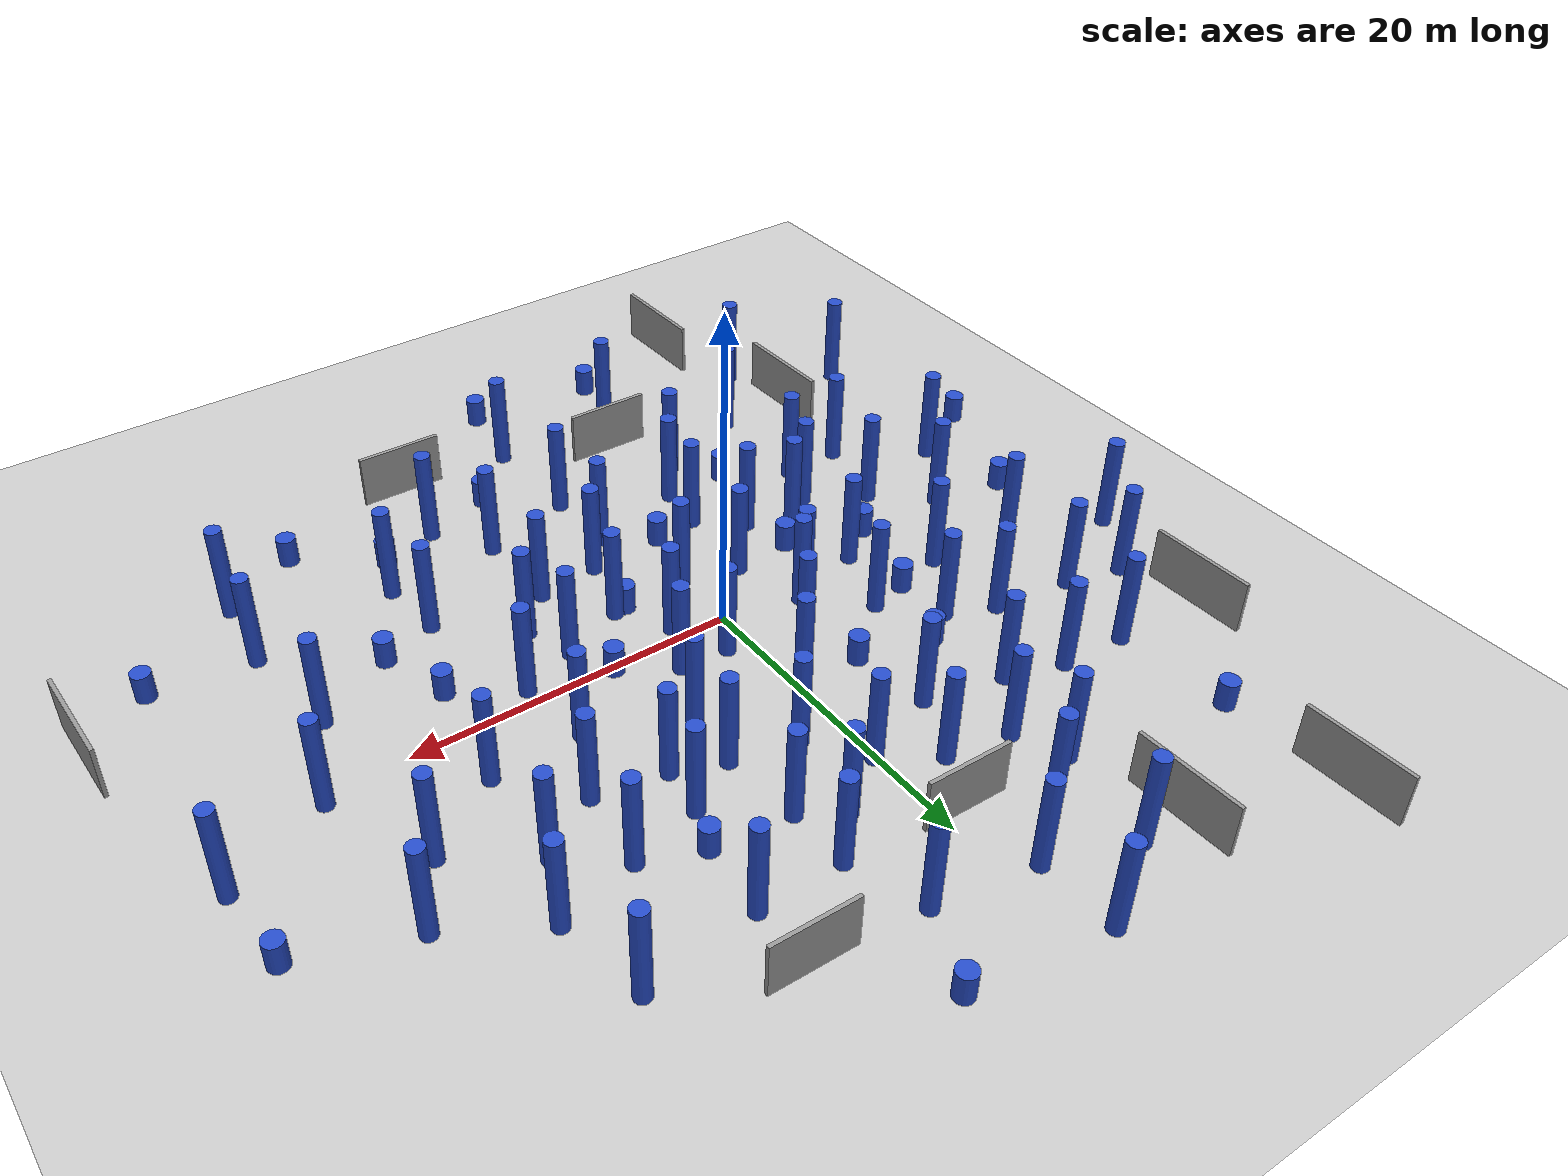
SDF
<sdf version="1.7">
 <world name="default">
  <physics type="ode">
   <ode>
    <solver>
     <type>quick</type>
     <iters>10</iters>
     <sor>1.3</sor>
     <use_dynamic_moi_rescaling>0</use_dynamic_moi_rescaling>
    </solver>
    <constraints>
     <cfm>1e-05</cfm>
     <erp>0.2</erp>
     <contact_max_correcting_vel>1000</contact_max_correcting_vel>
     <contact_surface_layer>0.01</contact_surface_layer>
    </constraints>
   </ode>
   <max_step_size>0.004</max_step_size>
   <real_time_factor>1</real_time_factor>
   <real_time_update_rate>250</real_time_update_rate>
   <gravity>0 0 -9.8066</gravity>
   <magnetic_field>6.0e-6 2.3e-5 -4.2e-5</magnetic_field>
  </physics>
  <light name="sun" type="directional">
   <cast_shadows>0</cast_shadows>
   <pose>0 0 100 0 -0 0</pose>
   <diffuse>0.8 0.8 0.8 1</diffuse>
   <specular>0.9 0.9 0.9 1</specular>
   <attenuation>
    <range>1000</range>
    <constant>0.9</constant>
    <linear>0.01</linear>
    <quadratic>0.001</quadratic>
   </attenuation>
   <direction>0.2 0.2 -0.9</direction>
   <spot><inner_angle>0</inner_angle><outer_angle>0</outer_angle><falloff>0</falloff></spot>
  </light>
  <scene><shadows>0</shadows><ambient>0.4 0.4 0.4 1</ambient><background>0.7 0.7 0.7 1</background></scene>
  <model name="ground_plane">
   <static>1</static>
   <link name="link">
    <collision name="collision">
     <geometry><plane><normal>0 0 1</normal><size>100 100</size></plane></geometry>
     <surface><friction><ode><mu>100</mu><mu2>50</mu2></ode></friction></surface>
    </collision>
    <visual name="visual">
     <cast_shadows>0</cast_shadows>
     <geometry><plane><normal>0 0 1</normal><size>100 100</size></plane></geometry>
     <material>
      <script><uri>file://media/materials/scripts/gazebo.material</uri><name>Gazebo/Grey</name></script>
     </material>
    </visual>
   </link>
  </model>
  <model name="unit_cylinder_1">
   <static>1</static>
   <pose>30.8945 8.63353 0.9 0 -0 0.001073</pose>
   <link name="link">
    <inertial>
     <mass>1</mass>
     <inertia><ixx>0.145833</ixx><ixy>0</ixy><ixz>0</ixz><iyy>0.145833</iyy><iyz>0</iyz><izz>0.125</izz></inertia>
    </inertial>
    <collision name="collision">
     <geometry><cylinder><radius>0.6</radius><length>1.8</length></cylinder></geometry>
     <surface><contact><collide_without_contact>1</collide_without_contact></contact></surface>
    </collision>
    <visual name="visual">
     <geometry><cylinder><radius>0.6</radius><length>1.8</length></cylinder></geometry>
     <material>
      <script><name>Gazebo/Blue</name><uri>file://media/materials/scripts/gazebo.material</uri></script>
     </material>
    </visual>
    <gravity>0</gravity>
   </link>
  </model>
  <model name="unit_box_0_0_clone_0_clone_clone_0_clone_clone_clone_clone_clone_clone">
   <static>1</static>
   <pose>-4.07635 -18.9992 1.66667 -2e-06 0.000226 1.55672</pose>
   <link name="link">
    <inertial>
     <mass>1</mass>
     <inertia>
      <ixx>0.166667</ixx>
      <ixy>0</ixy>
      <ixz>0</ixz>
      <iyy>0.166667</iyy>
      <iyz>0</iyz>
      <izz>0.166667</izz>
     </inertia>
    </inertial>
    <collision name="collision">
     <geometry><box><size>0.237691 5.28913 3.33454</size></box></geometry>
     <surface><contact><collide_without_contact>1</collide_without_contact></contact></surface>
    </collision>
    <visual name="visual">
     <geometry><box><size>0.237691 5.28913 3.33454</size></box></geometry>
     <material>
      <script><name>Gazebo/Grey</name><uri>file://media/materials/scripts/gazebo.material</uri></script>
     </material>
    </visual>
    <gravity>0</gravity>
   </link>
  </model>
  <model name="unit_box_0_0_clone_0_clone_clone_0_clone_clone_clone_clone_clone_clone_0">
   <static>1</static>
   <pose>-1.35623 19.251 1.66667 -2e-06 0.000226 1.55672</pose>
   <link name="link">
    <inertial>
     <mass>1</mass>
     <inertia>
      <ixx>0.166667</ixx>
      <ixy>0</ixy>
      <ixz>0</ixz>
      <iyy>0.166667</iyy>
      <iyz>0</iyz>
      <izz>0.166667</izz>
     </inertia>
    </inertial>
    <collision name="collision">
     <geometry><box><size>0.237691 5.28913 3.33454</size></box></geometry>
     <surface><contact><collide_without_contact>1</collide_without_contact></contact></surface>
    </collision>
    <visual name="visual">
     <geometry><box><size>0.237691 5.28913 3.33454</size></box></geometry>
     <material>
      <script><name>Gazebo/Grey</name><uri>file://media/materials/scripts/gazebo.material</uri></script>
     </material>
    </visual>
    <gravity>0</gravity>
   </link>
  </model>
  <model name="unit_box_0_0_clone_0_clone_clone_0_clone_clone_clone_clone_clone_clone_1">
   <static>1</static>
   <pose>9.37588 -22.2979 1.66667 -2e-06 0.000226 1.55672</pose>
   <link name="link">
    <inertial>
     <mass>1</mass>
     <inertia>
      <ixx>0.166667</ixx>
      <ixy>0</ixy>
      <ixz>0</ixz>
      <iyy>0.166667</iyy>
      <iyz>0</iyz>
      <izz>0.166667</izz>
     </inertia>
    </inertial>
    <collision name="collision">
     <geometry><box><size>0.237691 5.28913 3.33454</size></box></geometry>
     <surface><contact><collide_without_contact>1</collide_without_contact></contact></surface>
    </collision>
    <visual name="visual">
     <geometry><box><size>0.237691 5.28913 3.33454</size></box></geometry>
     <material>
      <script><name>Gazebo/Grey</name><uri>file://media/materials/scripts/gazebo.material</uri></script>
     </material>
    </visual>
    <gravity>0</gravity>
   </link>
  </model>
  <model name="unit_box_0_0_clone_0_clone_clone_0_clone_clone_clone_clone_clone_clone_2">
   <static>1</static>
   <pose>10.9902 22.7223 1.66667 -2e-06 0.000226 1.55672</pose>
   <link name="link">
    <inertial>
     <mass>1</mass>
     <inertia>
      <ixx>0.166667</ixx>
      <ixy>0</ixy>
      <ixz>0</ixz>
      <iyy>0.166667</iyy>
      <iyz>0</iyz>
      <izz>0.166667</izz>
     </inertia>
    </inertial>
    <collision name="collision">
     <geometry><box><size>0.237691 5.28913 3.33454</size></box></geometry>
     <surface><contact><collide_without_contact>1</collide_without_contact></contact></surface>
    </collision>
    <visual name="visual">
     <geometry><box><size>0.237691 5.28913 3.33454</size></box></geometry>
     <material>
      <script><name>Gazebo/Grey</name><uri>file://media/materials/scripts/gazebo.material</uri></script>
     </material>
    </visual>
    <gravity>0</gravity>
   </link>
  </model>
  <model name="unit_box_0_0_clone_0_clone_clone_0_clone_clone_clone">
   <static>1</static>
   <pose>-9.88058 25.7727 1.66667 -0.000226 6e-06 0.022264</pose>
   <link name="link">
    <inertial>
     <mass>1</mass>
     <inertia>
      <ixx>0.166667</ixx>
      <ixy>0</ixy>
      <ixz>0</ixz>
      <iyy>0.166667</iyy>
      <iyz>0</iyz>
      <izz>0.166667</izz>
     </inertia>
    </inertial>
    <collision name="collision">
     <geometry><box><size>0.237691 6.53987 3.33454</size></box></geometry>
     <surface><contact><collide_without_contact>1</collide_without_contact></contact></surface>
    </collision>
    <visual name="visual">
     <geometry><box><size>0.237691 6.53987 3.33454</size></box></geometry>
     <material>
      <script><name>Gazebo/Grey</name><uri>file://media/materials/scripts/gazebo.material</uri></script>
     </material>
    </visual>
    <gravity>0</gravity>
   </link>
  </model>
  <model name="unit_box_0_0_clone_0_clone_clone_0_clone_clone_clone_0">
   <static>1</static>
   <pose>34.0051 -9.5632 1.66667 -0.000226 6e-06 0.022264</pose>
   <link name="link">
    <inertial>
     <mass>1</mass>
     <inertia>
      <ixx>0.166667</ixx>
      <ixy>0</ixy>
      <ixz>0</ixz>
      <iyy>0.166667</iyy>
      <iyz>0</iyz>
      <izz>0.166667</izz>
     </inertia>
    </inertial>
    <collision name="collision">
     <geometry><box><size>0.237691 6.53987 3.33454</size></box></geometry>
     <surface><contact><collide_without_contact>1</collide_without_contact></contact></surface>
    </collision>
    <visual name="visual">
     <geometry><box><size>0.237691 6.53987 3.33454</size></box></geometry>
     <material>
      <script><name>Gazebo/Grey</name><uri>file://media/materials/scripts/gazebo.material</uri></script>
     </material>
    </visual>
    <gravity>0</gravity>
   </link>
  </model>
  <model name="unit_box_0_0_clone_0_clone_clone_0_clone_clone_clone_1">
   <static>1</static>
   <pose>-16.9775 -16.9385 1.66667 -0.000226 6e-06 0.022264</pose>
   <link name="link">
    <inertial>
     <mass>1</mass>
     <inertia>
      <ixx>0.166667</ixx>
      <ixy>0</ixy>
      <ixz>0</ixz>
      <iyy>0.166667</iyy>
      <iyz>0</iyz>
      <izz>0.166667</izz>
     </inertia>
    </inertial>
    <collision name="collision">
     <geometry><box><size>0.237691 6.53987 3.33454</size></box></geometry>
     <surface><contact><collide_without_contact>1</collide_without_contact></contact></surface>
    </collision>
    <visual name="visual">
     <geometry><box><size>0.237691 6.53987 3.33454</size></box></geometry>
     <material>
      <script><name>Gazebo/Grey</name><uri>file://media/materials/scripts/gazebo.material</uri></script>
     </material>
    </visual>
    <gravity>0</gravity>
   </link>
  </model>
  <model name="unit_box_0_0_clone_0_clone_clone_0_clone_clone_clone_2">
   <static>1</static>
   <pose>-23.5976 14.4859 1.66667 -0.000226 6e-06 0.022264</pose>
   <link name="link">
    <inertial>
     <mass>1</mass>
     <inertia>
      <ixx>0.166667</ixx>
      <ixy>0</ixy>
      <ixz>0</ixz>
      <iyy>0.166667</iyy>
      <iyz>0</iyz>
      <izz>0.166667</izz>
     </inertia>
    </inertial>
    <collision name="collision">
     <geometry><box><size>0.237691 6.53987 3.33454</size></box></geometry>
     <surface><contact><collide_without_contact>1</collide_without_contact></contact></surface>
    </collision>
    <visual name="visual">
     <geometry><box><size>0.237691 6.53987 3.33454</size></box></geometry>
     <material>
      <script><name>Gazebo/Grey</name><uri>file://media/materials/scripts/gazebo.material</uri></script>
     </material>
    </visual>
    <gravity>0</gravity>
   </link>
  </model>
  <model name="unit_box_0_0_clone_0_clone_clone_0_clone_clone_clone_3">
   <static>1</static>
   <pose>-18.4558 29.2742 1.66667 -0.000226 6e-06 0.022264</pose>
   <link name="link">
    <inertial>
     <mass>1</mass>
     <inertia>
      <ixx>0.166667</ixx>
      <ixy>0</ixy>
      <ixz>0</ixz>
      <iyy>0.166667</iyy>
      <iyz>0</iyz>
      <izz>0.166667</izz>
     </inertia>
    </inertial>
    <collision name="collision">
     <geometry><box><size>0.237691 6.53987 3.33454</size></box></geometry>
     <surface><contact><collide_without_contact>1</collide_without_contact></contact></surface>
    </collision>
    <visual name="visual">
     <geometry><box><size>0.237691 6.53987 3.33454</size></box></geometry>
     <material>
      <script><name>Gazebo/Grey</name><uri>file://media/materials/scripts/gazebo.material</uri></script>
     </material>
    </visual>
    <gravity>0</gravity>
   </link>
  </model>
  <model name="unit_box_0_0_clone_0_clone_clone_0_clone_clone_clone_4">
   <static>1</static>
   <pose>-13.7812 -27.768 1.66667 -0.000226 6e-06 0.022264</pose>
   <link name="link">
    <inertial>
     <mass>1</mass>
     <inertia>
      <ixx>0.166667</ixx>
      <ixy>0</ixy>
      <ixz>0</ixz>
      <iyy>0.166667</iyy>
      <iyz>0</iyz>
      <izz>0.166667</izz>
     </inertia>
    </inertial>
    <collision name="collision">
     <geometry><box><size>0.237691 6.53987 3.33454</size></box></geometry>
     <surface><contact><collide_without_contact>1</collide_without_contact></contact></surface>
    </collision>
    <visual name="visual">
     <geometry><box><size>0.237691 6.53987 3.33454</size></box></geometry>
     <material>
      <script><name>Gazebo/Grey</name><uri>file://media/materials/scripts/gazebo.material</uri></script>
     </material>
    </visual>
    <gravity>0</gravity>
   </link>
  </model>
  <model name="unit_cylinder_0_clone">
   <static>1</static>
   <pose>23.5724 -11.8027 3 0 -0 0.001073</pose>
   <link name="link">
    <inertial>
     <mass>1</mass>
     <inertia><ixx>0.145833</ixx><ixy>0</ixy><ixz>0</ixz><iyy>0.145833</iyy><iyz>0</iyz><izz>0.125</izz></inertia>
    </inertial>
    <collision name="collision">
     <geometry><cylinder><radius>0.5</radius><length>6</length></cylinder></geometry>
     <surface><contact><collide_without_contact>1</collide_without_contact></contact></surface>
    </collision>
    <visual name="visual">
     <geometry><cylinder><radius>0.5</radius><length>6</length></cylinder></geometry>
     <material>
      <script><name>Gazebo/Blue</name><uri>file://media/materials/scripts/gazebo.material</uri></script>
     </material>
    </visual>
    <gravity>0</gravity>
   </link>
  </model>
  <model name="unit_cylinder_0_clone_0">
   <static>1</static>
   <pose>19.2061 14.1082 3 0 -0 0.001073</pose>
   <link name="link">
    <inertial>
     <mass>1</mass>
     <inertia><ixx>0.145833</ixx><ixy>0</ixy><ixz>0</ixz><iyy>0.145833</iyy><iyz>0</iyz><izz>0.125</izz></inertia>
    </inertial>
    <collision name="collision">
     <geometry><cylinder><radius>0.5</radius><length>6</length></cylinder></geometry>
     <surface><contact><collide_without_contact>1</collide_without_contact></contact></surface>
    </collision>
    <visual name="visual">
     <geometry><cylinder><radius>0.5</radius><length>6</length></cylinder></geometry>
     <material>
      <script><name>Gazebo/Blue</name><uri>file://media/materials/scripts/gazebo.material</uri></script>
     </material>
    </visual>
    <gravity>0</gravity>
   </link>
  </model>
  <model name="unit_cylinder_0_clone_5">
   <static>1</static>
   <pose>17.29 3.83892 3 0 -0 0.001073</pose>
   <link name="link">
    <inertial>
     <mass>1</mass>
     <inertia><ixx>0.145833</ixx><ixy>0</ixy><ixz>0</ixz><iyy>0.145833</iyy><iyz>0</iyz><izz>0.125</izz></inertia>
    </inertial>
    <collision name="collision">
     <geometry><cylinder><radius>0.5</radius><length>6</length></cylinder></geometry>
     <surface><contact><collide_without_contact>1</collide_without_contact></contact></surface>
    </collision>
    <visual name="visual">
     <geometry><cylinder><radius>0.5</radius><length>6</length></cylinder></geometry>
     <material>
      <script><name>Gazebo/Blue</name><uri>file://media/materials/scripts/gazebo.material</uri></script>
     </material>
    </visual>
    <gravity>0</gravity>
   </link>
  </model>
  <model name="unit_cylinder_0_clone_10">
   <static>1</static>
   <pose>14.6533 -13.0732 3 0 -0 0.001073</pose>
   <link name="link">
    <inertial>
     <mass>1</mass>
     <inertia><ixx>0.145833</ixx><ixy>0</ixy><ixz>0</ixz><iyy>0.145833</iyy><iyz>0</iyz><izz>0.125</izz></inertia>
    </inertial>
    <collision name="collision">
     <geometry><cylinder><radius>0.5</radius><length>6</length></cylinder></geometry>
     <surface><contact><collide_without_contact>1</collide_without_contact></contact></surface>
    </collision>
    <visual name="visual">
     <geometry><cylinder><radius>0.5</radius><length>6</length></cylinder></geometry>
     <material>
      <script><name>Gazebo/Blue</name><uri>file://media/materials/scripts/gazebo.material</uri></script>
     </material>
    </visual>
    <gravity>0</gravity>
   </link>
  </model>
  <model name="unit_cylinder_0_clone_11">
   <static>1</static>
   <pose>-18.6647 9.01289 3 0 -0 0.001073</pose>
   <link name="link">
    <inertial>
     <mass>1</mass>
     <inertia><ixx>0.145833</ixx><ixy>0</ixy><ixz>0</ixz><iyy>0.145833</iyy><iyz>0</iyz><izz>0.125</izz></inertia>
    </inertial>
    <collision name="collision">
     <geometry><cylinder><radius>0.5</radius><length>6</length></cylinder></geometry>
     <surface><contact><collide_without_contact>1</collide_without_contact></contact></surface>
    </collision>
    <visual name="visual">
     <geometry><cylinder><radius>0.5</radius><length>6</length></cylinder></geometry>
     <material>
      <script><name>Gazebo/Blue</name><uri>file://media/materials/scripts/gazebo.material</uri></script>
     </material>
    </visual>
    <gravity>0</gravity>
   </link>
  </model>
  <model name="unit_cylinder_0_clone_15">
   <static>1</static>
   <pose>24.4702 11 3 0 -0 0.001073</pose>
   <link name="link">
    <inertial>
     <mass>1</mass>
     <inertia><ixx>0.145833</ixx><ixy>0</ixy><ixz>0</ixz><iyy>0.145833</iyy><iyz>0</iyz><izz>0.125</izz></inertia>
    </inertial>
    <collision name="collision">
     <geometry><cylinder><radius>0.5</radius><length>6</length></cylinder></geometry>
     <surface><contact><collide_without_contact>1</collide_without_contact></contact></surface>
    </collision>
    <visual name="visual">
     <geometry><cylinder><radius>0.5</radius><length>6</length></cylinder></geometry>
     <material>
      <script><name>Gazebo/Blue</name><uri>file://media/materials/scripts/gazebo.material</uri></script>
     </material>
    </visual>
    <gravity>0</gravity>
   </link>
  </model>
  <model name="unit_cylinder_0_clone_17">
   <static>1</static>
   <pose>-15.8005 -21.5961 3 0 -0 0.001073</pose>
   <link name="link">
    <inertial>
     <mass>1</mass>
     <inertia><ixx>0.145833</ixx><ixy>0</ixy><ixz>0</ixz><iyy>0.145833</iyy><iyz>0</iyz><izz>0.125</izz></inertia>
    </inertial>
    <collision name="collision">
     <geometry><cylinder><radius>0.5</radius><length>6</length></cylinder></geometry>
     <surface><contact><collide_without_contact>1</collide_without_contact></contact></surface>
    </collision>
    <visual name="visual">
     <geometry><cylinder><radius>0.5</radius><length>6</length></cylinder></geometry>
     <material>
      <script><name>Gazebo/Blue</name><uri>file://media/materials/scripts/gazebo.material</uri></script>
     </material>
    </visual>
    <gravity>0</gravity>
   </link>
  </model>
  <model name="unit_cylinder_0_clone_18">
   <static>1</static>
   <pose>-21.0697 -6.42311 3 0 -0 0.001073</pose>
   <link name="link">
    <inertial>
     <mass>1</mass>
     <inertia><ixx>0.145833</ixx><ixy>0</ixy><ixz>0</ixz><iyy>0.145833</iyy><iyz>0</iyz><izz>0.125</izz></inertia>
    </inertial>
    <collision name="collision">
     <geometry><cylinder><radius>0.5</radius><length>6</length></cylinder></geometry>
     <surface><contact><collide_without_contact>1</collide_without_contact></contact></surface>
    </collision>
    <visual name="visual">
     <geometry><cylinder><radius>0.5</radius><length>6</length></cylinder></geometry>
     <material>
      <script><name>Gazebo/Blue</name><uri>file://media/materials/scripts/gazebo.material</uri></script>
     </material>
    </visual>
    <gravity>0</gravity>
   </link>
  </model>
  <model name="unit_cylinder_0_clone_53">
   <static>1</static>
   <pose>25.011 0.609466 3 0 -0 0.001073</pose>
   <link name="link">
    <inertial>
     <mass>1</mass>
     <inertia><ixx>0.145833</ixx><ixy>0</ixy><ixz>0</ixz><iyy>0.145833</iyy><iyz>0</iyz><izz>0.125</izz></inertia>
    </inertial>
    <collision name="collision">
     <geometry><cylinder><radius>0.5</radius><length>6</length></cylinder></geometry>
     <surface><contact><collide_without_contact>1</collide_without_contact></contact></surface>
    </collision>
    <visual name="visual">
     <geometry><cylinder><radius>0.5</radius><length>6</length></cylinder></geometry>
     <material>
      <script><name>Gazebo/Blue</name><uri>file://media/materials/scripts/gazebo.material</uri></script>
     </material>
    </visual>
    <gravity>0</gravity>
   </link>
  </model>
  <model name="unit_cylinder_0_clone_55">
   <static>1</static>
   <pose>-6.46237 -6.58507 3 0 -0 0.001073</pose>
   <link name="link">
    <inertial>
     <mass>1</mass>
     <inertia><ixx>0.145833</ixx><ixy>0</ixy><ixz>0</ixz><iyy>0.145833</iyy><iyz>0</iyz><izz>0.125</izz></inertia>
    </inertial>
    <collision name="collision">
     <geometry><cylinder><radius>0.5</radius><length>6</length></cylinder></geometry>
     <surface><contact><collide_without_contact>1</collide_without_contact></contact></surface>
    </collision>
    <visual name="visual">
     <geometry><cylinder><radius>0.5</radius><length>6</length></cylinder></geometry>
     <material>
      <script><name>Gazebo/Blue</name><uri>file://media/materials/scripts/gazebo.material</uri></script>
     </material>
    </visual>
    <gravity>0</gravity>
   </link>
  </model>
  <model name="unit_cylinder_0_clone_56">
   <static>1</static>
   <pose>6.1738 6.18159 3 0 -0 0.001073</pose>
   <link name="link">
    <inertial>
     <mass>1</mass>
     <inertia><ixx>0.145833</ixx><ixy>0</ixy><ixz>0</ixz><iyy>0.145833</iyy><iyz>0</iyz><izz>0.125</izz></inertia>
    </inertial>
    <collision name="collision">
     <geometry><cylinder><radius>0.5</radius><length>6</length></cylinder></geometry>
     <surface><contact><collide_without_contact>1</collide_without_contact></contact></surface>
    </collision>
    <visual name="visual">
     <geometry><cylinder><radius>0.5</radius><length>6</length></cylinder></geometry>
     <material>
      <script><name>Gazebo/Blue</name><uri>file://media/materials/scripts/gazebo.material</uri></script>
     </material>
    </visual>
    <gravity>0</gravity>
   </link>
  </model>
  <model name="unit_cylinder_0_clone_57">
   <static>1</static>
   <pose>7.55385 -7.7575 3 0 -0 0.001073</pose>
   <link name="link">
    <inertial>
     <mass>1</mass>
     <inertia><ixx>0.145833</ixx><ixy>0</ixy><ixz>0</ixz><iyy>0.145833</iyy><iyz>0</iyz><izz>0.125</izz></inertia>
    </inertial>
    <collision name="collision">
     <geometry><cylinder><radius>0.5</radius><length>6</length></cylinder></geometry>
     <surface><contact><collide_without_contact>1</collide_without_contact></contact></surface>
    </collision>
    <visual name="visual">
     <geometry><cylinder><radius>0.5</radius><length>6</length></cylinder></geometry>
     <material>
      <script><name>Gazebo/Blue</name><uri>file://media/materials/scripts/gazebo.material</uri></script>
     </material>
    </visual>
    <gravity>0</gravity>
   </link>
  </model>
  <model name="unit_cylinder_0_clone_58">
   <static>1</static>
   <pose>-9.77888 13.1498 3 0 -0 0.001073</pose>
   <link name="link">
    <inertial>
     <mass>1</mass>
     <inertia><ixx>0.145833</ixx><ixy>0</ixy><ixz>0</ixz><iyy>0.145833</iyy><iyz>0</iyz><izz>0.125</izz></inertia>
    </inertial>
    <collision name="collision">
     <geometry><cylinder><radius>0.5</radius><length>6</length></cylinder></geometry>
     <surface><contact><collide_without_contact>1</collide_without_contact></contact></surface>
    </collision>
    <visual name="visual">
     <geometry><cylinder><radius>0.5</radius><length>6</length></cylinder></geometry>
     <material>
      <script><name>Gazebo/Blue</name><uri>file://media/materials/scripts/gazebo.material</uri></script>
     </material>
    </visual>
    <gravity>0</gravity>
   </link>
  </model>
  <model name="unit_cylinder_0_clone_59">
   <static>1</static>
   <pose>2 -15 3 0 -0 0.001073</pose>
   <link name="link">
    <inertial>
     <mass>1</mass>
     <inertia><ixx>0.145833</ixx><ixy>0</ixy><ixz>0</ixz><iyy>0.145833</iyy><iyz>0</iyz><izz>0.125</izz></inertia>
    </inertial>
    <collision name="collision">
     <geometry><cylinder><radius>0.5</radius><length>6</length></cylinder></geometry>
     <surface><contact><collide_without_contact>1</collide_without_contact></contact></surface>
    </collision>
    <visual name="visual">
     <geometry><cylinder><radius>0.5</radius><length>6</length></cylinder></geometry>
     <material>
      <script><name>Gazebo/Blue</name><uri>file://media/materials/scripts/gazebo.material</uri></script>
     </material>
    </visual>
    <gravity>0</gravity>
   </link>
  </model>
  <model name="unit_cylinder_1_clone_3">
   <static>1</static>
   <pose>10.7828 14.1577 0.9 0 -0 0.001073</pose>
   <link name="link">
    <inertial>
     <mass>1</mass>
     <inertia><ixx>0.145833</ixx><ixy>0</ixy><ixz>0</ixz><iyy>0.145833</iyy><iyz>0</iyz><izz>0.125</izz></inertia>
    </inertial>
    <collision name="collision">
     <geometry><cylinder><radius>0.6</radius><length>1.8</length></cylinder></geometry>
     <surface><contact><collide_without_contact>1</collide_without_contact></contact></surface>
    </collision>
    <visual name="visual">
     <geometry><cylinder><radius>0.6</radius><length>1.8</length></cylinder></geometry>
     <material>
      <script><name>Gazebo/Blue</name><uri>file://media/materials/scripts/gazebo.material</uri></script>
     </material>
    </visual>
    <gravity>0</gravity>
   </link>
  </model>
  <model name="unit_cylinder_1_clone_4">
   <static>1</static>
   <pose>6.362 27.7652 0.9 0 -0 0.001073</pose>
   <link name="link">
    <inertial>
     <mass>1</mass>
     <inertia><ixx>0.145833</ixx><ixy>0</ixy><ixz>0</ixz><iyy>0.145833</iyy><iyz>0</iyz><izz>0.125</izz></inertia>
    </inertial>
    <collision name="collision">
     <geometry><cylinder><radius>0.6</radius><length>1.8</length></cylinder></geometry>
     <surface><contact><collide_without_contact>1</collide_without_contact></contact></surface>
    </collision>
    <visual name="visual">
     <geometry><cylinder><radius>0.6</radius><length>1.8</length></cylinder></geometry>
     <material>
      <script><name>Gazebo/Blue</name><uri>file://media/materials/scripts/gazebo.material</uri></script>
     </material>
    </visual>
    <gravity>0</gravity>
   </link>
  </model>
  <model name="unit_cylinder_1_clone_5">
   <static>1</static>
   <pose>29.6778 -12.511 0.9 0 -0 0.001073</pose>
   <link name="link">
    <inertial>
     <mass>1</mass>
     <inertia><ixx>0.145833</ixx><ixy>0</ixy><ixz>0</ixz><iyy>0.145833</iyy><iyz>0</iyz><izz>0.125</izz></inertia>
    </inertial>
    <collision name="collision">
     <geometry><cylinder><radius>0.6</radius><length>1.8</length></cylinder></geometry>
     <surface><contact><collide_without_contact>1</collide_without_contact></contact></surface>
    </collision>
    <visual name="visual">
     <geometry><cylinder><radius>0.6</radius><length>1.8</length></cylinder></geometry>
     <material>
      <script><name>Gazebo/Blue</name><uri>file://media/materials/scripts/gazebo.material</uri></script>
     </material>
    </visual>
    <gravity>0</gravity>
   </link>
  </model>
  <model name="unit_cylinder_1_clone_7">
   <static>1</static>
   <pose>18.3931 -19.4937 0.9 0 -0 0.001073</pose>
   <link name="link">
    <inertial>
     <mass>1</mass>
     <inertia><ixx>0.145833</ixx><ixy>0</ixy><ixz>0</ixz><iyy>0.145833</iyy><iyz>0</iyz><izz>0.125</izz></inertia>
    </inertial>
    <collision name="collision">
     <geometry><cylinder><radius>0.6</radius><length>1.8</length></cylinder></geometry>
     <surface><contact><collide_without_contact>1</collide_without_contact></contact></surface>
    </collision>
    <visual name="visual">
     <geometry><cylinder><radius>0.6</radius><length>1.8</length></cylinder></geometry>
     <material>
      <script><name>Gazebo/Blue</name><uri>file://media/materials/scripts/gazebo.material</uri></script>
     </material>
    </visual>
    <gravity>0</gravity>
   </link>
  </model>
  <model name="unit_cylinder_1_clone_8">
   <static>1</static>
   <pose>17.6395 -7.71205 0.9 0 -0 0.001073</pose>
   <link name="link">
    <inertial>
     <mass>1</mass>
     <inertia><ixx>0.145833</ixx><ixy>0</ixy><ixz>0</ixz><iyy>0.145833</iyy><iyz>0</iyz><izz>0.125</izz></inertia>
    </inertial>
    <collision name="collision">
     <geometry><cylinder><radius>0.6</radius><length>1.8</length></cylinder></geometry>
     <surface><contact><collide_without_contact>1</collide_without_contact></contact></surface>
    </collision>
    <visual name="visual">
     <geometry><cylinder><radius>0.6</radius><length>1.8</length></cylinder></geometry>
     <material>
      <script><name>Gazebo/Blue</name><uri>file://media/materials/scripts/gazebo.material</uri></script>
     </material>
    </visual>
    <gravity>0</gravity>
   </link>
  </model>
  <model name="unit_cylinder_1_clone_9">
   <static>1</static>
   <pose>7.53493 0.253658 0.9 0 -0 0.001073</pose>
   <link name="link">
    <inertial>
     <mass>1</mass>
     <inertia><ixx>0.145833</ixx><ixy>0</ixy><ixz>0</ixz><iyy>0.145833</iyy><iyz>0</iyz><izz>0.125</izz></inertia>
    </inertial>
    <collision name="collision">
     <geometry><cylinder><radius>0.6</radius><length>1.8</length></cylinder></geometry>
     <surface><contact><collide_without_contact>1</collide_without_contact></contact></surface>
    </collision>
    <visual name="visual">
     <geometry><cylinder><radius>0.6</radius><length>1.8</length></cylinder></geometry>
     <material>
      <script><name>Gazebo/Blue</name><uri>file://media/materials/scripts/gazebo.material</uri></script>
     </material>
    </visual>
    <gravity>0</gravity>
   </link>
  </model>
  <model name="unit_cylinder_1_clone_10">
   <static>1</static>
   <pose>-8.78291 8.32938 0.9 0 -0 0.001073</pose>
   <link name="link">
    <inertial>
     <mass>1</mass>
     <inertia><ixx>0.145833</ixx><ixy>0</ixy><ixz>0</ixz><iyy>0.145833</iyy><iyz>0</iyz><izz>0.125</izz></inertia>
    </inertial>
    <collision name="collision">
     <geometry><cylinder><radius>0.6</radius><length>1.8</length></cylinder></geometry>
     <surface><contact><collide_without_contact>1</collide_without_contact></contact></surface>
    </collision>
    <visual name="visual">
     <geometry><cylinder><radius>0.6</radius><length>1.8</length></cylinder></geometry>
     <material>
      <script><name>Gazebo/Blue</name><uri>file://media/materials/scripts/gazebo.material</uri></script>
     </material>
    </visual>
    <gravity>0</gravity>
   </link>
  </model>
  <model name="unit_cylinder_1_clone_11">
   <static>1</static>
   <pose>-12.0224 -2.00419 0.9 0 -0 0.001073</pose>
   <link name="link">
    <inertial>
     <mass>1</mass>
     <inertia><ixx>0.145833</ixx><ixy>0</ixy><ixz>0</ixz><iyy>0.145833</iyy><iyz>0</iyz><izz>0.125</izz></inertia>
    </inertial>
    <collision name="collision">
     <geometry><cylinder><radius>0.6</radius><length>1.8</length></cylinder></geometry>
     <surface><contact><collide_without_contact>1</collide_without_contact></contact></surface>
    </collision>
    <visual name="visual">
     <geometry><cylinder><radius>0.6</radius><length>1.8</length></cylinder></geometry>
     <material>
      <script><name>Gazebo/Blue</name><uri>file://media/materials/scripts/gazebo.material</uri></script>
     </material>
    </visual>
    <gravity>0</gravity>
   </link>
  </model>
  <model name="unit_cylinder_1_clone_12">
   <static>1</static>
   <pose>-8.28835 -12.0056 0.9 0 -0 0.001073</pose>
   <link name="link">
    <inertial>
     <mass>1</mass>
     <inertia><ixx>0.145833</ixx><ixy>0</ixy><ixz>0</ixz><iyy>0.145833</iyy><iyz>0</iyz><izz>0.125</izz></inertia>
    </inertial>
    <collision name="collision">
     <geometry><cylinder><radius>0.6</radius><length>1.8</length></cylinder></geometry>
     <surface><contact><collide_without_contact>1</collide_without_contact></contact></surface>
    </collision>
    <visual name="visual">
     <geometry><cylinder><radius>0.6</radius><length>1.8</length></cylinder></geometry>
     <material>
      <script><name>Gazebo/Blue</name><uri>file://media/materials/scripts/gazebo.material</uri></script>
     </material>
    </visual>
    <gravity>0</gravity>
   </link>
  </model>
  <model name="unit_cylinder_1_clone_13">
   <static>1</static>
   <pose>-18.1805 21.517 0.9 0 -0 0.001073</pose>
   <link name="link">
    <inertial>
     <mass>1</mass>
     <inertia><ixx>0.145833</ixx><ixy>0</ixy><ixz>0</ixz><iyy>0.145833</iyy><iyz>0</iyz><izz>0.125</izz></inertia>
    </inertial>
    <collision name="collision">
     <geometry><cylinder><radius>0.6</radius><length>1.8</length></cylinder></geometry>
     <surface><contact><collide_without_contact>1</collide_without_contact></contact></surface>
    </collision>
    <visual name="visual">
     <geometry><cylinder><radius>0.6</radius><length>1.8</length></cylinder></geometry>
     <material>
      <script><name>Gazebo/Blue</name><uri>file://media/materials/scripts/gazebo.material</uri></script>
     </material>
    </visual>
    <gravity>0</gravity>
   </link>
  </model>
  <model name="unit_cylinder_1_clone_19">
   <static>1</static>
   <pose>1.55407 -26.9495 0.9 0 -0 0.001073</pose>
   <link name="link">
    <inertial>
     <mass>1</mass>
     <inertia><ixx>0.145833</ixx><ixy>0</ixy><ixz>0</ixz><iyy>0.145833</iyy><iyz>0</iyz><izz>0.125</izz></inertia>
    </inertial>
    <collision name="collision">
     <geometry><cylinder><radius>0.6</radius><length>1.8</length></cylinder></geometry>
     <surface><contact><collide_without_contact>1</collide_without_contact></contact></surface>
    </collision>
    <visual name="visual">
     <geometry><cylinder><radius>0.6</radius><length>1.8</length></cylinder></geometry>
     <material>
      <script><name>Gazebo/Blue</name><uri>file://media/materials/scripts/gazebo.material</uri></script>
     </material>
    </visual>
    <gravity>0</gravity>
   </link>
  </model>
  <gravity>0 0 -9.8</gravity>
  <magnetic_field>6e-06 2.3e-05 -4.2e-05</magnetic_field>
  <atmosphere type="adiabatic"/>
  <spherical_coordinates>
   <surface_model>EARTH_WGS84</surface_model>
   <latitude_deg>0</latitude_deg>
   <longitude_deg>0</longitude_deg>
   <elevation>0</elevation>
   <heading_deg>0</heading_deg>
  </spherical_coordinates>
  <model name="unit_cylinder_0_clone_3_clone">
   <static>1</static>
   <pose>-5.44686 0.623967 3 0 -0 0.001073</pose>
   <link name="link">
    <inertial>
     <mass>1</mass>
     <inertia><ixx>0.145833</ixx><ixy>0</ixy><ixz>0</ixz><iyy>0.145833</iyy><iyz>0</iyz><izz>0.125</izz></inertia>
    </inertial>
    <collision name="collision">
     <geometry><cylinder><radius>0.5</radius><length>6</length></cylinder></geometry>
     <surface><contact><collide_without_contact>1</collide_without_contact></contact></surface>
    </collision>
    <visual name="visual">
     <geometry><cylinder><radius>0.5</radius><length>6</length></cylinder></geometry>
     <material>
      <script><name>Gazebo/Blue</name><uri>file://media/materials/scripts/gazebo.material</uri></script>
     </material>
    </visual>
    <gravity>0</gravity>
   </link>
  </model>
  <model name="unit_cylinder_0_clone_3_clone_0">
   <static>1</static>
   <pose>-0.521379 6.93964 3 0 -0 0.001073</pose>
   <link name="link">
    <inertial>
     <mass>1</mass>
     <inertia><ixx>0.145833</ixx><ixy>0</ixy><ixz>0</ixz><iyy>0.145833</iyy><iyz>0</iyz><izz>0.125</izz></inertia>
    </inertial>
    <collision name="collision">
     <geometry><cylinder><radius>0.5</radius><length>6</length></cylinder></geometry>
     <surface><contact><collide_without_contact>1</collide_without_contact></contact></surface>
    </collision>
    <visual name="visual">
     <geometry><cylinder><radius>0.5</radius><length>6</length></cylinder></geometry>
     <material>
      <script><name>Gazebo/Blue</name><uri>file://media/materials/scripts/gazebo.material</uri></script>
     </material>
    </visual>
    <gravity>0</gravity>
   </link>
  </model>
  <model name="unit_cylinder_0_clone_3_clone_1">
   <static>1</static>
   <pose>1.79769 -10.4468 3 0 -0 0.001073</pose>
   <link name="link">
    <inertial>
     <mass>1</mass>
     <inertia><ixx>0.145833</ixx><ixy>0</ixy><ixz>0</ixz><iyy>0.145833</iyy><iyz>0</iyz><izz>0.125</izz></inertia>
    </inertial>
    <collision name="collision">
     <geometry><cylinder><radius>0.5</radius><length>6</length></cylinder></geometry>
     <surface><contact><collide_without_contact>1</collide_without_contact></contact></surface>
    </collision>
    <visual name="visual">
     <geometry><cylinder><radius>0.5</radius><length>6</length></cylinder></geometry>
     <material>
      <script><name>Gazebo/Blue</name><uri>file://media/materials/scripts/gazebo.material</uri></script>
     </material>
    </visual>
    <gravity>0</gravity>
   </link>
  </model>
  <model name="unit_cylinder_0_clone_3_clone_2">
   <static>1</static>
   <pose>-13.6112 2.87137 3 0 -0 0.001073</pose>
   <link name="link">
    <inertial>
     <mass>1</mass>
     <inertia><ixx>0.145833</ixx><ixy>0</ixy><ixz>0</ixz><iyy>0.145833</iyy><iyz>0</iyz><izz>0.125</izz></inertia>
    </inertial>
    <collision name="collision">
     <geometry><cylinder><radius>0.5</radius><length>6</length></cylinder></geometry>
     <surface><contact><collide_without_contact>1</collide_without_contact></contact></surface>
    </collision>
    <visual name="visual">
     <geometry><cylinder><radius>0.5</radius><length>6</length></cylinder></geometry>
     <material>
      <script><name>Gazebo/Blue</name><uri>file://media/materials/scripts/gazebo.material</uri></script>
     </material>
    </visual>
    <gravity>0</gravity>
   </link>
  </model>
  <model name="unit_cylinder_0_clone_3_clone_3">
   <static>1</static>
   <pose>-15.8614 -9.81445 3 0 -0 0.001073</pose>
   <link name="link">
    <inertial>
     <mass>1</mass>
     <inertia><ixx>0.145833</ixx><ixy>0</ixy><ixz>0</ixz><iyy>0.145833</iyy><iyz>0</iyz><izz>0.125</izz></inertia>
    </inertial>
    <collision name="collision">
     <geometry><cylinder><radius>0.5</radius><length>6</length></cylinder></geometry>
     <surface><contact><collide_without_contact>1</collide_without_contact></contact></surface>
    </collision>
    <visual name="visual">
     <geometry><cylinder><radius>0.5</radius><length>6</length></cylinder></geometry>
     <material>
      <script><name>Gazebo/Blue</name><uri>file://media/materials/scripts/gazebo.material</uri></script>
     </material>
    </visual>
    <gravity>0</gravity>
   </link>
  </model>
  <model name="unit_cylinder_0_clone_3_clone_4">
   <static>1</static>
   <pose>-6.04746 -14.462 3 0 -0 0.001073</pose>
   <link name="link">
    <inertial>
     <mass>1</mass>
     <inertia><ixx>0.145833</ixx><ixy>0</ixy><ixz>0</ixz><iyy>0.145833</iyy><iyz>0</iyz><izz>0.125</izz></inertia>
    </inertial>
    <collision name="collision">
     <geometry><cylinder><radius>0.5</radius><length>6</length></cylinder></geometry>
     <surface><contact><collide_without_contact>1</collide_without_contact></contact></surface>
    </collision>
    <visual name="visual">
     <geometry><cylinder><radius>0.5</radius><length>6</length></cylinder></geometry>
     <material>
      <script><name>Gazebo/Blue</name><uri>file://media/materials/scripts/gazebo.material</uri></script>
     </material>
    </visual>
    <gravity>0</gravity>
   </link>
  </model>
  <model name="unit_cylinder_0_clone_3_clone_5">
   <static>1</static>
   <pose>0.129351 13.9177 3 0 -0 0.001073</pose>
   <link name="link">
    <inertial>
     <mass>1</mass>
     <inertia><ixx>0.145833</ixx><ixy>0</ixy><ixz>0</ixz><iyy>0.145833</iyy><iyz>0</iyz><izz>0.125</izz></inertia>
    </inertial>
    <collision name="collision">
     <geometry><cylinder><radius>0.5</radius><length>6</length></cylinder></geometry>
     <surface><contact><collide_without_contact>1</collide_without_contact></contact></surface>
    </collision>
    <visual name="visual">
     <geometry><cylinder><radius>0.5</radius><length>6</length></cylinder></geometry>
     <material>
      <script><name>Gazebo/Blue</name><uri>file://media/materials/scripts/gazebo.material</uri></script>
     </material>
    </visual>
    <gravity>0</gravity>
   </link>
  </model>
  <model name="unit_cylinder_0_clone_3_clone_6">
   <static>1</static>
   <pose>12.3759 -0.977729 3 0 -0 0.001073</pose>
   <link name="link">
    <inertial>
     <mass>1</mass>
     <inertia><ixx>0.145833</ixx><ixy>0</ixy><ixz>0</ixz><iyy>0.145833</iyy><iyz>0</iyz><izz>0.125</izz></inertia>
    </inertial>
    <collision name="collision">
     <geometry><cylinder><radius>0.5</radius><length>6</length></cylinder></geometry>
     <surface><contact><collide_without_contact>1</collide_without_contact></contact></surface>
    </collision>
    <visual name="visual">
     <geometry><cylinder><radius>0.5</radius><length>6</length></cylinder></geometry>
     <material>
      <script><name>Gazebo/Blue</name><uri>file://media/materials/scripts/gazebo.material</uri></script>
     </material>
    </visual>
    <gravity>0</gravity>
   </link>
  </model>
  <model name="unit_cylinder_0_clone_3_clone_7">
   <static>1</static>
   <pose>17.5051 10.2438 3 0 -0 0.001073</pose>
   <link name="link">
    <inertial>
     <mass>1</mass>
     <inertia><ixx>0.145833</ixx><ixy>0</ixy><ixz>0</ixz><iyy>0.145833</iyy><iyz>0</iyz><izz>0.125</izz></inertia>
    </inertial>
    <collision name="collision">
     <geometry><cylinder><radius>0.5</radius><length>6</length></cylinder></geometry>
     <surface><contact><collide_without_contact>1</collide_without_contact></contact></surface>
    </collision>
    <visual name="visual">
     <geometry><cylinder><radius>0.5</radius><length>6</length></cylinder></geometry>
     <material>
      <script><name>Gazebo/Blue</name><uri>file://media/materials/scripts/gazebo.material</uri></script>
     </material>
    </visual>
    <gravity>0</gravity>
   </link>
  </model>
  <model name="unit_cylinder_0_clone_3_clone_8">
   <static>1</static>
   <pose>18.2052 19.6027 3 0 -0 0.001073</pose>
   <link name="link">
    <inertial>
     <mass>1</mass>
     <inertia><ixx>0.145833</ixx><ixy>0</ixy><ixz>0</ixz><iyy>0.145833</iyy><iyz>0</iyz><izz>0.125</izz></inertia>
    </inertial>
    <collision name="collision">
     <geometry><cylinder><radius>0.5</radius><length>6</length></cylinder></geometry>
     <surface><contact><collide_without_contact>1</collide_without_contact></contact></surface>
    </collision>
    <visual name="visual">
     <geometry><cylinder><radius>0.5</radius><length>6</length></cylinder></geometry>
     <material>
      <script><name>Gazebo/Blue</name><uri>file://media/materials/scripts/gazebo.material</uri></script>
     </material>
    </visual>
    <gravity>0</gravity>
   </link>
  </model>
  <model name="unit_cylinder_0_clone_3_clone_9">
   <static>1</static>
   <pose>22.5834 -5.04922 3 0 -0 0.001073</pose>
   <link name="link">
    <inertial>
     <mass>1</mass>
     <inertia><ixx>0.145833</ixx><ixy>0</ixy><ixz>0</ixz><iyy>0.145833</iyy><iyz>0</iyz><izz>0.125</izz></inertia>
    </inertial>
    <collision name="collision">
     <geometry><cylinder><radius>0.5</radius><length>6</length></cylinder></geometry>
     <surface><contact><collide_without_contact>1</collide_without_contact></contact></surface>
    </collision>
    <visual name="visual">
     <geometry><cylinder><radius>0.5</radius><length>6</length></cylinder></geometry>
     <material>
      <script><name>Gazebo/Blue</name><uri>file://media/materials/scripts/gazebo.material</uri></script>
     </material>
    </visual>
    <gravity>0</gravity>
   </link>
  </model>
  <model name="unit_cylinder_0_clone_3_clone_10">
   <static>1</static>
   <pose>-5.87324 -22.4043 3 0 -0 0.001073</pose>
   <link name="link">
    <inertial>
     <mass>1</mass>
     <inertia><ixx>0.145833</ixx><ixy>0</ixy><ixz>0</ixz><iyy>0.145833</iyy><iyz>0</iyz><izz>0.125</izz></inertia>
    </inertial>
    <collision name="collision">
     <geometry><cylinder><radius>0.5</radius><length>6</length></cylinder></geometry>
     <surface><contact><collide_without_contact>1</collide_without_contact></contact></surface>
    </collision>
    <visual name="visual">
     <geometry><cylinder><radius>0.5</radius><length>6</length></cylinder></geometry>
     <material>
      <script><name>Gazebo/Blue</name><uri>file://media/materials/scripts/gazebo.material</uri></script>
     </material>
    </visual>
    <gravity>0</gravity>
   </link>
  </model>
  <model name="unit_cylinder_0_clone_3_clone_12">
   <static>1</static>
   <pose>11.172 18.673 3 0 -0 0.001073</pose>
   <link name="link">
    <inertial>
     <mass>1</mass>
     <inertia><ixx>0.145833</ixx><ixy>0</ixy><ixz>0</ixz><iyy>0.145833</iyy><iyz>0</iyz><izz>0.125</izz></inertia>
    </inertial>
    <collision name="collision">
     <geometry><cylinder><radius>0.5</radius><length>6</length></cylinder></geometry>
     <surface><contact><collide_without_contact>1</collide_without_contact></contact></surface>
    </collision>
    <visual name="visual">
     <geometry><cylinder><radius>0.5</radius><length>6</length></cylinder></geometry>
     <material>
      <script><name>Gazebo/Blue</name><uri>file://media/materials/scripts/gazebo.material</uri></script>
     </material>
    </visual>
    <gravity>0</gravity>
   </link>
  </model>
  <model name="unit_cylinder_0_clone_3_clone_13">
   <static>1</static>
   <pose>-1.8244 24.1865 3 0 -0 0.001073</pose>
   <link name="link">
    <inertial>
     <mass>1</mass>
     <inertia><ixx>0.145833</ixx><ixy>0</ixy><ixz>0</ixz><iyy>0.145833</iyy><iyz>0</iyz><izz>0.125</izz></inertia>
    </inertial>
    <collision name="collision">
     <geometry><cylinder><radius>0.5</radius><length>6</length></cylinder></geometry>
     <surface><contact><collide_without_contact>1</collide_without_contact></contact></surface>
    </collision>
    <visual name="visual">
     <geometry><cylinder><radius>0.5</radius><length>6</length></cylinder></geometry>
     <material>
      <script><name>Gazebo/Blue</name><uri>file://media/materials/scripts/gazebo.material</uri></script>
     </material>
    </visual>
    <gravity>0</gravity>
   </link>
  </model>
  <model name="unit_cylinder_0_clone_3_clone_15">
   <static>1</static>
   <pose>-19.0398 3.44436 3 0 -0 0.001073</pose>
   <link name="link">
    <inertial>
     <mass>1</mass>
     <inertia><ixx>0.145833</ixx><ixy>0</ixy><ixz>0</ixz><iyy>0.145833</iyy><iyz>0</iyz><izz>0.125</izz></inertia>
    </inertial>
    <collision name="collision">
     <geometry><cylinder><radius>0.5</radius><length>6</length></cylinder></geometry>
     <surface><contact><collide_without_contact>1</collide_without_contact></contact></surface>
    </collision>
    <visual name="visual">
     <geometry><cylinder><radius>0.5</radius><length>6</length></cylinder></geometry>
     <material>
      <script><name>Gazebo/Blue</name><uri>file://media/materials/scripts/gazebo.material</uri></script>
     </material>
    </visual>
    <gravity>0</gravity>
   </link>
  </model>
  <model name="unit_cylinder_1_clone_19_clone">
   <static>1</static>
   <pose>4.08634 -4.05232 0.9 0 -0 0.001073</pose>
   <link name="link">
    <inertial>
     <mass>1</mass>
     <inertia><ixx>0.145833</ixx><ixy>0</ixy><ixz>0</ixz><iyy>0.145833</iyy><iyz>0</iyz><izz>0.125</izz></inertia>
    </inertial>
    <collision name="collision">
     <geometry><cylinder><radius>0.6</radius><length>1.8</length></cylinder></geometry>
     <surface><contact><collide_without_contact>1</collide_without_contact></contact></surface>
    </collision>
    <visual name="visual">
     <geometry><cylinder><radius>0.6</radius><length>1.8</length></cylinder></geometry>
     <material>
      <script><name>Gazebo/Blue</name><uri>file://media/materials/scripts/gazebo.material</uri></script>
     </material>
    </visual>
    <gravity>0</gravity>
   </link>
  </model>
  <model name="unit_cylinder_1_clone_19_clone_0">
   <static>1</static>
   <pose>-7.20572 -3.59145 0.9 0 -0 0.001073</pose>
   <link name="link">
    <inertial>
     <mass>1</mass>
     <inertia><ixx>0.145833</ixx><ixy>0</ixy><ixz>0</ixz><iyy>0.145833</iyy><iyz>0</iyz><izz>0.125</izz></inertia>
    </inertial>
    <collision name="collision">
     <geometry><cylinder><radius>0.6</radius><length>1.8</length></cylinder></geometry>
     <surface><contact><collide_without_contact>1</collide_without_contact></contact></surface>
    </collision>
    <visual name="visual">
     <geometry><cylinder><radius>0.6</radius><length>1.8</length></cylinder></geometry>
     <material>
      <script><name>Gazebo/Blue</name><uri>file://media/materials/scripts/gazebo.material</uri></script>
     </material>
    </visual>
    <gravity>0</gravity>
   </link>
  </model>
  <model name="unit_cylinder_1_clone_19_clone_1">
   <static>1</static>
   <pose>-4.17583 7.23667 0.9 0 -0 0.001073</pose>
   <link name="link">
    <inertial>
     <mass>1</mass>
     <inertia><ixx>0.145833</ixx><ixy>0</ixy><ixz>0</ixz><iyy>0.145833</iyy><iyz>0</iyz><izz>0.125</izz></inertia>
    </inertial>
    <collision name="collision">
     <geometry><cylinder><radius>0.6</radius><length>1.8</length></cylinder></geometry>
     <surface><contact><collide_without_contact>1</collide_without_contact></contact></surface>
    </collision>
    <visual name="visual">
     <geometry><cylinder><radius>0.6</radius><length>1.8</length></cylinder></geometry>
     <material>
      <script><name>Gazebo/Blue</name><uri>file://media/materials/scripts/gazebo.material</uri></script>
     </material>
    </visual>
    <gravity>0</gravity>
   </link>
  </model>
  <model name="unit_cylinder_1_clone_19_clone_2">
   <static>1</static>
   <pose>16.2049 -3.41918 0.9 0 -0 0.001073</pose>
   <link name="link">
    <inertial>
     <mass>1</mass>
     <inertia><ixx>0.145833</ixx><ixy>0</ixy><ixz>0</ixz><iyy>0.145833</iyy><iyz>0</iyz><izz>0.125</izz></inertia>
    </inertial>
    <collision name="collision">
     <geometry><cylinder><radius>0.6</radius><length>1.8</length></cylinder></geometry>
     <surface><contact><collide_without_contact>1</collide_without_contact></contact></surface>
    </collision>
    <visual name="visual">
     <geometry><cylinder><radius>0.6</radius><length>1.8</length></cylinder></geometry>
     <material>
      <script><name>Gazebo/Blue</name><uri>file://media/materials/scripts/gazebo.material</uri></script>
     </material>
    </visual>
    <gravity>0</gravity>
   </link>
  </model>
  <model name="unit_cylinder_1_clone_19_clone_3">
   <static>1</static>
   <pose>5.80019 -18.2504 0.9 0 -0 0.001073</pose>
   <link name="link">
    <inertial>
     <mass>1</mass>
     <inertia><ixx>0.145833</ixx><ixy>0</ixy><ixz>0</ixz><iyy>0.145833</iyy><iyz>0</iyz><izz>0.125</izz></inertia>
    </inertial>
    <collision name="collision">
     <geometry><cylinder><radius>0.6</radius><length>1.8</length></cylinder></geometry>
     <surface><contact><collide_without_contact>1</collide_without_contact></contact></surface>
    </collision>
    <visual name="visual">
     <geometry><cylinder><radius>0.6</radius><length>1.8</length></cylinder></geometry>
     <material>
      <script><name>Gazebo/Blue</name><uri>file://media/materials/scripts/gazebo.material</uri></script>
     </material>
    </visual>
    <gravity>0</gravity>
   </link>
  </model>
  <model name="unit_cylinder_1_clone_19_clone_5">
   <static>1</static>
   <pose>-6.57664 -26.1556 0.9 0 -0 0.001073</pose>
   <link name="link">
    <inertial>
     <mass>1</mass>
     <inertia><ixx>0.145833</ixx><ixy>0</ixy><ixz>0</ixz><iyy>0.145833</iyy><iyz>0</iyz><izz>0.125</izz></inertia>
    </inertial>
    <collision name="collision">
     <geometry><cylinder><radius>0.6</radius><length>1.8</length></cylinder></geometry>
     <surface><contact><collide_without_contact>1</collide_without_contact></contact></surface>
    </collision>
    <visual name="visual">
     <geometry><cylinder><radius>0.6</radius><length>1.8</length></cylinder></geometry>
     <material>
      <script><name>Gazebo/Blue</name><uri>file://media/materials/scripts/gazebo.material</uri></script>
     </material>
    </visual>
    <gravity>0</gravity>
   </link>
  </model>
  <model name="unit_cylinder_1_clone_19_clone_7">
   <static>1</static>
   <pose>-22.4422 -1 0.9 0 -0 0.001073</pose>
   <link name="link">
    <inertial>
     <mass>1</mass>
     <inertia><ixx>0.145833</ixx><ixy>0</ixy><ixz>0</ixz><iyy>0.145833</iyy><iyz>0</iyz><izz>0.125</izz></inertia>
    </inertial>
    <collision name="collision">
     <geometry><cylinder><radius>0.6</radius><length>1.8</length></cylinder></geometry>
     <surface><contact><collide_without_contact>1</collide_without_contact></contact></surface>
    </collision>
    <visual name="visual">
     <geometry><cylinder><radius>0.6</radius><length>1.8</length></cylinder></geometry>
     <material>
      <script><name>Gazebo/Blue</name><uri>file://media/materials/scripts/gazebo.material</uri></script>
     </material>
    </visual>
    <gravity>0</gravity>
   </link>
  </model>
  <model name="unit_cylinder_1_clone_19_clone_8">
   <static>1</static>
   <pose>-25.4789 -8.73219 0.9 0 -0 0.001073</pose>
   <link name="link">
    <inertial>
     <mass>1</mass>
     <inertia><ixx>0.145833</ixx><ixy>0</ixy><ixz>0</ixz><iyy>0.145833</iyy><iyz>0</iyz><izz>0.125</izz></inertia>
    </inertial>
    <collision name="collision">
     <geometry><cylinder><radius>0.6</radius><length>1.8</length></cylinder></geometry>
     <surface><contact><collide_without_contact>1</collide_without_contact></contact></surface>
    </collision>
    <visual name="visual">
     <geometry><cylinder><radius>0.6</radius><length>1.8</length></cylinder></geometry>
     <material>
      <script><name>Gazebo/Blue</name><uri>file://media/materials/scripts/gazebo.material</uri></script>
     </material>
    </visual>
    <gravity>0</gravity>
   </link>
  </model>
  <model name="unit_cylinder_1_clone_19_clone_12">
   <static>1</static>
   <pose>13.6276 -15.9206 0.9 0 -0 0.001073</pose>
   <link name="link">
    <inertial>
     <mass>1</mass>
     <inertia><ixx>0.145833</ixx><ixy>0</ixy><ixz>0</ixz><iyy>0.145833</iyy><iyz>0</iyz><izz>0.125</izz></inertia>
    </inertial>
    <collision name="collision">
     <geometry><cylinder><radius>0.6</radius><length>1.8</length></cylinder></geometry>
     <surface><contact><collide_without_contact>1</collide_without_contact></contact></surface>
    </collision>
    <visual name="visual">
     <geometry><cylinder><radius>0.6</radius><length>1.8</length></cylinder></geometry>
     <material>
      <script><name>Gazebo/Blue</name><uri>file://media/materials/scripts/gazebo.material</uri></script>
     </material>
    </visual>
    <gravity>0</gravity>
   </link>
  </model>
  <model name="unit_cylinder_1_clone_19_clone_13">
   <static>1</static>
   <pose>-1.07028 -8.48174 0.9 0 -0 0.001073</pose>
   <link name="link">
    <inertial>
     <mass>1</mass>
     <inertia><ixx>0.145833</ixx><ixy>0</ixy><ixz>0</ixz><iyy>0.145833</iyy><iyz>0</iyz><izz>0.125</izz></inertia>
    </inertial>
    <collision name="collision">
     <geometry><cylinder><radius>0.6</radius><length>1.8</length></cylinder></geometry>
     <surface><contact><collide_without_contact>1</collide_without_contact></contact></surface>
    </collision>
    <visual name="visual">
     <geometry><cylinder><radius>0.6</radius><length>1.8</length></cylinder></geometry>
     <material>
      <script><name>Gazebo/Blue</name><uri>file://media/materials/scripts/gazebo.material</uri></script>
     </material>
    </visual>
    <gravity>0</gravity>
   </link>
  </model>
  <model name="unit_cylinder_1_clone_19_clone_14">
   <static>1</static>
   <pose>-10.4201 3.62822 0.9 0 -0 0.001073</pose>
   <link name="link">
    <inertial>
     <mass>1</mass>
     <inertia><ixx>0.145833</ixx><ixy>0</ixy><ixz>0</ixz><iyy>0.145833</iyy><iyz>0</iyz><izz>0.125</izz></inertia>
    </inertial>
    <collision name="collision">
     <geometry><cylinder><radius>0.6</radius><length>1.8</length></cylinder></geometry>
     <surface><contact><collide_without_contact>1</collide_without_contact></contact></surface>
    </collision>
    <visual name="visual">
     <geometry><cylinder><radius>0.6</radius><length>1.8</length></cylinder></geometry>
     <material>
      <script><name>Gazebo/Blue</name><uri>file://media/materials/scripts/gazebo.material</uri></script>
     </material>
    </visual>
    <gravity>0</gravity>
   </link>
  </model>
  <model name="unit_cylinder_0_clone_3_clone_clone">
   <static>1</static>
   <pose>3.66917 -8.20938 3 0 -0 0.001073</pose>
   <link name="link">
    <inertial>
     <mass>1</mass>
     <inertia><ixx>0.145833</ixx><ixy>0</ixy><ixz>0</ixz><iyy>0.145833</iyy><iyz>0</iyz><izz>0.125</izz></inertia>
    </inertial>
    <collision name="collision">
     <geometry><cylinder><radius>0.5</radius><length>6</length></cylinder></geometry>
     <surface><contact><collide_without_contact>1</collide_without_contact></contact></surface>
    </collision>
    <visual name="visual">
     <geometry><cylinder><radius>0.5</radius><length>6</length></cylinder></geometry>
     <material>
      <script><name>Gazebo/Blue</name><uri>file://media/materials/scripts/gazebo.material</uri></script>
     </material>
    </visual>
    <gravity>0</gravity>
   </link>
  </model>
  <model name="unit_cylinder_0_clone_3_clone_clone_0">
   <static>1</static>
   <pose>-12.133 -9.66191 3 0 -0 0.001073</pose>
   <link name="link">
    <inertial>
     <mass>1</mass>
     <inertia><ixx>0.145833</ixx><ixy>0</ixy><ixz>0</ixz><iyy>0.145833</iyy><iyz>0</iyz><izz>0.125</izz></inertia>
    </inertial>
    <collision name="collision">
     <geometry><cylinder><radius>0.5</radius><length>6</length></cylinder></geometry>
     <surface><contact><collide_without_contact>1</collide_without_contact></contact></surface>
    </collision>
    <visual name="visual">
     <geometry><cylinder><radius>0.5</radius><length>6</length></cylinder></geometry>
     <material>
      <script><name>Gazebo/Blue</name><uri>file://media/materials/scripts/gazebo.material</uri></script>
     </material>
    </visual>
    <gravity>0</gravity>
   </link>
  </model>
  <model name="unit_cylinder_0_clone_3_clone_clone_1">
   <static>1</static>
   <pose>-13.6781 8.34432 3 0 -0 0.001073</pose>
   <link name="link">
    <inertial>
     <mass>1</mass>
     <inertia><ixx>0.145833</ixx><ixy>0</ixy><ixz>0</ixz><iyy>0.145833</iyy><iyz>0</iyz><izz>0.125</izz></inertia>
    </inertial>
    <collision name="collision">
     <geometry><cylinder><radius>0.5</radius><length>6</length></cylinder></geometry>
     <surface><contact><collide_without_contact>1</collide_without_contact></contact></surface>
    </collision>
    <visual name="visual">
     <geometry><cylinder><radius>0.5</radius><length>6</length></cylinder></geometry>
     <material>
      <script><name>Gazebo/Blue</name><uri>file://media/materials/scripts/gazebo.material</uri></script>
     </material>
    </visual>
    <gravity>0</gravity>
   </link>
  </model>
  <model name="unit_cylinder_0_clone_3_clone_clone_2">
   <static>1</static>
   <pose>9.50136 8.69754 3 0 -0 0.001073</pose>
   <link name="link">
    <inertial>
     <mass>1</mass>
     <inertia><ixx>0.145833</ixx><ixy>0</ixy><ixz>0</ixz><iyy>0.145833</iyy><iyz>0</iyz><izz>0.125</izz></inertia>
    </inertial>
    <collision name="collision">
     <geometry><cylinder><radius>0.5</radius><length>6</length></cylinder></geometry>
     <surface><contact><collide_without_contact>1</collide_without_contact></contact></surface>
    </collision>
    <visual name="visual">
     <geometry><cylinder><radius>0.5</radius><length>6</length></cylinder></geometry>
     <material>
      <script><name>Gazebo/Blue</name><uri>file://media/materials/scripts/gazebo.material</uri></script>
     </material>
    </visual>
    <gravity>0</gravity>
   </link>
  </model>
  <model name="unit_cylinder_0_clone_3_clone_clone_3">
   <static>1</static>
   <pose>6.0049 14.709 3 0 -0 0.001073</pose>
   <link name="link">
    <inertial>
     <mass>1</mass>
     <inertia><ixx>0.145833</ixx><ixy>0</ixy><ixz>0</ixz><iyy>0.145833</iyy><iyz>0</iyz><izz>0.125</izz></inertia>
    </inertial>
    <collision name="collision">
     <geometry><cylinder><radius>0.5</radius><length>6</length></cylinder></geometry>
     <surface><contact><collide_without_contact>1</collide_without_contact></contact></surface>
    </collision>
    <visual name="visual">
     <geometry><cylinder><radius>0.5</radius><length>6</length></cylinder></geometry>
     <material>
      <script><name>Gazebo/Blue</name><uri>file://media/materials/scripts/gazebo.material</uri></script>
     </material>
    </visual>
    <gravity>0</gravity>
   </link>
  </model>
  <model name="unit_cylinder_0_clone_3_clone_clone_4">
   <static>1</static>
   <pose>-6.96125 16.6675 3 0 -0 0.001073</pose>
   <link name="link">
    <inertial>
     <mass>1</mass>
     <inertia><ixx>0.145833</ixx><ixy>0</ixy><ixz>0</ixz><iyy>0.145833</iyy><iyz>0</iyz><izz>0.125</izz></inertia>
    </inertial>
    <collision name="collision">
     <geometry><cylinder><radius>0.5</radius><length>6</length></cylinder></geometry>
     <surface><contact><collide_without_contact>1</collide_without_contact></contact></surface>
    </collision>
    <visual name="visual">
     <geometry><cylinder><radius>0.5</radius><length>6</length></cylinder></geometry>
     <material>
      <script><name>Gazebo/Blue</name><uri>file://media/materials/scripts/gazebo.material</uri></script>
     </material>
    </visual>
    <gravity>0</gravity>
   </link>
  </model>
  <model name="unit_cylinder_0_clone_3_clone_clone_5">
   <static>1</static>
   <pose>0.048161 -4.13589 3 0 -0 0.001073</pose>
   <link name="link">
    <inertial>
     <mass>1</mass>
     <inertia><ixx>0.145833</ixx><ixy>0</ixy><ixz>0</ixz><iyy>0.145833</iyy><iyz>0</iyz><izz>0.125</izz></inertia>
    </inertial>
    <collision name="collision">
     <geometry><cylinder><radius>0.5</radius><length>6</length></cylinder></geometry>
     <surface><contact><collide_without_contact>1</collide_without_contact></contact></surface>
    </collision>
    <visual name="visual">
     <geometry><cylinder><radius>0.5</radius><length>6</length></cylinder></geometry>
     <material>
      <script><name>Gazebo/Blue</name><uri>file://media/materials/scripts/gazebo.material</uri></script>
     </material>
    </visual>
    <gravity>0</gravity>
   </link>
  </model>
  <model name="unit_cylinder_0_clone_3_clone_clone_6">
   <static>1</static>
   <pose>4.41585 2.29177 3 0 -0 0.001073</pose>
   <link name="link">
    <inertial>
     <mass>1</mass>
     <inertia><ixx>0.145833</ixx><ixy>0</ixy><ixz>0</ixz><iyy>0.145833</iyy><iyz>0</iyz><izz>0.125</izz></inertia>
    </inertial>
    <collision name="collision">
     <geometry><cylinder><radius>0.5</radius><length>6</length></cylinder></geometry>
     <surface><contact><collide_without_contact>1</collide_without_contact></contact></surface>
    </collision>
    <visual name="visual">
     <geometry><cylinder><radius>0.5</radius><length>6</length></cylinder></geometry>
     <material>
      <script><name>Gazebo/Blue</name><uri>file://media/materials/scripts/gazebo.material</uri></script>
     </material>
    </visual>
    <gravity>0</gravity>
   </link>
  </model>
  <model name="unit_cylinder_0_clone_3_clone_clone_7">
   <static>1</static>
   <pose>-2.84647 4.08185 3 0 -0 0.001073</pose>
   <link name="link">
    <inertial>
     <mass>1</mass>
     <inertia><ixx>0.145833</ixx><ixy>0</ixy><ixz>0</ixz><iyy>0.145833</iyy><iyz>0</iyz><izz>0.125</izz></inertia>
    </inertial>
    <collision name="collision">
     <geometry><cylinder><radius>0.5</radius><length>6</length></cylinder></geometry>
     <surface><contact><collide_without_contact>1</collide_without_contact></contact></surface>
    </collision>
    <visual name="visual">
     <geometry><cylinder><radius>0.5</radius><length>6</length></cylinder></geometry>
     <material>
      <script><name>Gazebo/Blue</name><uri>file://media/materials/scripts/gazebo.material</uri></script>
     </material>
    </visual>
    <gravity>0</gravity>
   </link>
  </model>
  <model name="unit_cylinder_0_clone_3_clone_clone_8">
   <static>1</static>
   <pose>2.52709 10.6665 3 0 -0 0.001073</pose>
   <link name="link">
    <inertial>
     <mass>1</mass>
     <inertia><ixx>0.145833</ixx><ixy>0</ixy><ixz>0</ixz><iyy>0.145833</iyy><iyz>0</iyz><izz>0.125</izz></inertia>
    </inertial>
    <collision name="collision">
     <geometry><cylinder><radius>0.5</radius><length>6</length></cylinder></geometry>
     <surface><contact><collide_without_contact>1</collide_without_contact></contact></surface>
    </collision>
    <visual name="visual">
     <geometry><cylinder><radius>0.5</radius><length>6</length></cylinder></geometry>
     <material>
      <script><name>Gazebo/Blue</name><uri>file://media/materials/scripts/gazebo.material</uri></script>
     </material>
    </visual>
    <gravity>0</gravity>
   </link>
  </model>
  <model name="unit_cylinder_0_clone_3_clone_clone_9">
   <static>1</static>
   <pose>-4.87347 12.0297 3 0 -0 0.001073</pose>
   <link name="link">
    <inertial>
     <mass>1</mass>
     <inertia><ixx>0.145833</ixx><ixy>0</ixy><ixz>0</ixz><iyy>0.145833</iyy><iyz>0</iyz><izz>0.125</izz></inertia>
    </inertial>
    <collision name="collision">
     <geometry><cylinder><radius>0.5</radius><length>6</length></cylinder></geometry>
     <surface><contact><collide_without_contact>1</collide_without_contact></contact></surface>
    </collision>
    <visual name="visual">
     <geometry><cylinder><radius>0.5</radius><length>6</length></cylinder></geometry>
     <material>
      <script><name>Gazebo/Blue</name><uri>file://media/materials/scripts/gazebo.material</uri></script>
     </material>
    </visual>
    <gravity>0</gravity>
   </link>
  </model>
  <model name="unit_cylinder_0_clone_3_clone_clone_10">
   <static>1</static>
   <pose>-14.631 -4.6998 3 0 -0 0.001073</pose>
   <link name="link">
    <inertial>
     <mass>1</mass>
     <inertia><ixx>0.145833</ixx><ixy>0</ixy><ixz>0</ixz><iyy>0.145833</iyy><iyz>0</iyz><izz>0.125</izz></inertia>
    </inertial>
    <collision name="collision">
     <geometry><cylinder><radius>0.5</radius><length>6</length></cylinder></geometry>
     <surface><contact><collide_without_contact>1</collide_without_contact></contact></surface>
    </collision>
    <visual name="visual">
     <geometry><cylinder><radius>0.5</radius><length>6</length></cylinder></geometry>
     <material>
      <script><name>Gazebo/Blue</name><uri>file://media/materials/scripts/gazebo.material</uri></script>
     </material>
    </visual>
    <gravity>0</gravity>
   </link>
  </model>
  <model name="unit_cylinder_0_clone_3_clone_clone_11">
   <static>1</static>
   <pose>-4.254 -11.918 3 0 -0 0.001073</pose>
   <link name="link">
    <inertial>
     <mass>1</mass>
     <inertia><ixx>0.145833</ixx><ixy>0</ixy><ixz>0</ixz><iyy>0.145833</iyy><iyz>0</iyz><izz>0.125</izz></inertia>
    </inertial>
    <collision name="collision">
     <geometry><cylinder><radius>0.5</radius><length>6</length></cylinder></geometry>
     <surface><contact><collide_without_contact>1</collide_without_contact></contact></surface>
    </collision>
    <visual name="visual">
     <geometry><cylinder><radius>0.5</radius><length>6</length></cylinder></geometry>
     <material>
      <script><name>Gazebo/Blue</name><uri>file://media/materials/scripts/gazebo.material</uri></script>
     </material>
    </visual>
    <gravity>0</gravity>
   </link>
  </model>
  <model name="unit_cylinder_0_clone_3_clone_clone_12">
   <static>1</static>
   <pose>11.7531 3.70857 3 0 -0 0.001073</pose>
   <link name="link">
    <inertial>
     <mass>1</mass>
     <inertia><ixx>0.145833</ixx><ixy>0</ixy><ixz>0</ixz><iyy>0.145833</iyy><iyz>0</iyz><izz>0.125</izz></inertia>
    </inertial>
    <collision name="collision">
     <geometry><cylinder><radius>0.5</radius><length>6</length></cylinder></geometry>
     <surface><contact><collide_without_contact>1</collide_without_contact></contact></surface>
    </collision>
    <visual name="visual">
     <geometry><cylinder><radius>0.5</radius><length>6</length></cylinder></geometry>
     <material>
      <script><name>Gazebo/Blue</name><uri>file://media/materials/scripts/gazebo.material</uri></script>
     </material>
    </visual>
    <gravity>0</gravity>
   </link>
  </model>
  <model name="unit_cylinder_0_clone_3_clone_clone_13">
   <static>1</static>
   <pose>9.93828 -5.22638 3 0 -0 0.001073</pose>
   <link name="link">
    <inertial>
     <mass>1</mass>
     <inertia><ixx>0.145833</ixx><ixy>0</ixy><ixz>0</ixz><iyy>0.145833</iyy><iyz>0</iyz><izz>0.125</izz></inertia>
    </inertial>
    <collision name="collision">
     <geometry><cylinder><radius>0.5</radius><length>6</length></cylinder></geometry>
     <surface><contact><collide_without_contact>1</collide_without_contact></contact></surface>
    </collision>
    <visual name="visual">
     <geometry><cylinder><radius>0.5</radius><length>6</length></cylinder></geometry>
     <material>
      <script><name>Gazebo/Blue</name><uri>file://media/materials/scripts/gazebo.material</uri></script>
     </material>
    </visual>
    <gravity>0</gravity>
   </link>
  </model>
  <model name="unit_cylinder_0_clone_3_clone_clone_14">
   <static>1</static>
   <pose>5.93731 18.5962 3 0 -0 0.001073</pose>
   <link name="link">
    <inertial>
     <mass>1</mass>
     <inertia><ixx>0.145833</ixx><ixy>0</ixy><ixz>0</ixz><iyy>0.145833</iyy><iyz>0</iyz><izz>0.125</izz></inertia>
    </inertial>
    <collision name="collision">
     <geometry><cylinder><radius>0.5</radius><length>6</length></cylinder></geometry>
     <surface><contact><collide_without_contact>1</collide_without_contact></contact></surface>
    </collision>
    <visual name="visual">
     <geometry><cylinder><radius>0.5</radius><length>6</length></cylinder></geometry>
     <material>
      <script><name>Gazebo/Blue</name><uri>file://media/materials/scripts/gazebo.material</uri></script>
     </material>
    </visual>
    <gravity>0</gravity>
   </link>
  </model>
  <model name="unit_cylinder_0_clone_3_clone_clone_15">
   <static>1</static>
   <pose>-7.9678 4.19694 3 0 -0 0.001073</pose>
   <link name="link">
    <inertial>
     <mass>1</mass>
     <inertia><ixx>0.145833</ixx><ixy>0</ixy><ixz>0</ixz><iyy>0.145833</iyy><iyz>0</iyz><izz>0.125</izz></inertia>
    </inertial>
    <collision name="collision">
     <geometry><cylinder><radius>0.5</radius><length>6</length></cylinder></geometry>
     <surface><contact><collide_without_contact>1</collide_without_contact></contact></surface>
    </collision>
    <visual name="visual">
     <geometry><cylinder><radius>0.5</radius><length>6</length></cylinder></geometry>
     <material>
      <script><name>Gazebo/Blue</name><uri>file://media/materials/scripts/gazebo.material</uri></script>
     </material>
    </visual>
    <gravity>0</gravity>
   </link>
  </model>
  <model name="unit_cylinder_0_clone_3_clone_clone_16">
   <static>1</static>
   <pose>-12.1437 -16.7808 3 0 -0 0.001073</pose>
   <link name="link">
    <inertial>
     <mass>1</mass>
     <inertia><ixx>0.145833</ixx><ixy>0</ixy><ixz>0</ixz><iyy>0.145833</iyy><iyz>0</iyz><izz>0.125</izz></inertia>
    </inertial>
    <collision name="collision">
     <geometry><cylinder><radius>0.5</radius><length>6</length></cylinder></geometry>
     <surface><contact><collide_without_contact>1</collide_without_contact></contact></surface>
    </collision>
    <visual name="visual">
     <geometry><cylinder><radius>0.5</radius><length>6</length></cylinder></geometry>
     <material>
      <script><name>Gazebo/Blue</name><uri>file://media/materials/scripts/gazebo.material</uri></script>
     </material>
    </visual>
    <gravity>0</gravity>
   </link>
  </model>
  <model name="unit_cylinder_0_clone_3_clone_clone_17">
   <static>1</static>
   <pose>-13.3455 14.2455 3 0 -0 0.001073</pose>
   <link name="link">
    <inertial>
     <mass>1</mass>
     <inertia><ixx>0.145833</ixx><ixy>0</ixy><ixz>0</ixz><iyy>0.145833</iyy><iyz>0</iyz><izz>0.125</izz></inertia>
    </inertial>
    <collision name="collision">
     <geometry><cylinder><radius>0.5</radius><length>6</length></cylinder></geometry>
     <surface><contact><collide_without_contact>1</collide_without_contact></contact></surface>
    </collision>
    <visual name="visual">
     <geometry><cylinder><radius>0.5</radius><length>6</length></cylinder></geometry>
     <material>
      <script><name>Gazebo/Blue</name><uri>file://media/materials/scripts/gazebo.material</uri></script>
     </material>
    </visual>
    <gravity>0</gravity>
   </link>
  </model>
  <model name="unit_cylinder_0_clone_3_clone_clone_18">
   <static>1</static>
   <pose>-17.9554 -1.92572 3 0 -0 0.001073</pose>
   <link name="link">
    <inertial>
     <mass>1</mass>
     <inertia><ixx>0.145833</ixx><ixy>0</ixy><ixz>0</ixz><iyy>0.145833</iyy><iyz>0</iyz><izz>0.125</izz></inertia>
    </inertial>
    <collision name="collision">
     <geometry><cylinder><radius>0.5</radius><length>6</length></cylinder></geometry>
     <surface><contact><collide_without_contact>1</collide_without_contact></contact></surface>
    </collision>
    <visual name="visual">
     <geometry><cylinder><radius>0.5</radius><length>6</length></cylinder></geometry>
     <material>
      <script><name>Gazebo/Blue</name><uri>file://media/materials/scripts/gazebo.material</uri></script>
     </material>
    </visual>
    <gravity>0</gravity>
   </link>
  </model>
  <model name="unit_cylinder_0_clone_3_clone_clone_19">
   <static>1</static>
   <pose>10.1252 -16.8794 3 0 -0 0.001073</pose>
   <link name="link">
    <inertial>
     <mass>1</mass>
     <inertia><ixx>0.145833</ixx><ixy>0</ixy><ixz>0</ixz><iyy>0.145833</iyy><iyz>0</iyz><izz>0.125</izz></inertia>
    </inertial>
    <collision name="collision">
     <geometry><cylinder><radius>0.5</radius><length>6</length></cylinder></geometry>
     <surface><contact><collide_without_contact>1</collide_without_contact></contact></surface>
    </collision>
    <visual name="visual">
     <geometry><cylinder><radius>0.5</radius><length>6</length></cylinder></geometry>
     <material>
      <script><name>Gazebo/Blue</name><uri>file://media/materials/scripts/gazebo.material</uri></script>
     </material>
    </visual>
    <gravity>0</gravity>
   </link>
  </model>
  <model name="unit_cylinder_0_clone_3_clone_clone_20">
   <static>1</static>
   <pose>22.1323 7.06268 3 0 -0 0.001073</pose>
   <link name="link">
    <inertial>
     <mass>1</mass>
     <inertia><ixx>0.145833</ixx><ixy>0</ixy><ixz>0</ixz><iyy>0.145833</iyy><iyz>0</iyz><izz>0.125</izz></inertia>
    </inertial>
    <collision name="collision">
     <geometry><cylinder><radius>0.5</radius><length>6</length></cylinder></geometry>
     <surface><contact><collide_without_contact>1</collide_without_contact></contact></surface>
    </collision>
    <visual name="visual">
     <geometry><cylinder><radius>0.5</radius><length>6</length></cylinder></geometry>
     <material>
      <script><name>Gazebo/Blue</name><uri>file://media/materials/scripts/gazebo.material</uri></script>
     </material>
    </visual>
    <gravity>0</gravity>
   </link>
  </model>
  <model name="unit_cylinder_0_clone_3_clone_clone_21">
   <static>1</static>
   <pose>14.3016 12.8562 3 0 -0 0.001073</pose>
   <link name="link">
    <inertial>
     <mass>1</mass>
     <inertia><ixx>0.145833</ixx><ixy>0</ixy><ixz>0</ixz><iyy>0.145833</iyy><iyz>0</iyz><izz>0.125</izz></inertia>
    </inertial>
    <collision name="collision">
     <geometry><cylinder><radius>0.5</radius><length>6</length></cylinder></geometry>
     <surface><contact><collide_without_contact>1</collide_without_contact></contact></surface>
    </collision>
    <visual name="visual">
     <geometry><cylinder><radius>0.5</radius><length>6</length></cylinder></geometry>
     <material>
      <script><name>Gazebo/Blue</name><uri>file://media/materials/scripts/gazebo.material</uri></script>
     </material>
    </visual>
    <gravity>0</gravity>
   </link>
  </model>
  <model name="unit_cylinder_0_clone_3_clone_clone_22">
   <static>1</static>
   <pose>4.34476 23.1529 3 0 -0 0.001073</pose>
   <link name="link">
    <inertial>
     <mass>1</mass>
     <inertia><ixx>0.145833</ixx><ixy>0</ixy><ixz>0</ixz><iyy>0.145833</iyy><iyz>0</iyz><izz>0.125</izz></inertia>
    </inertial>
    <collision name="collision">
     <geometry><cylinder><radius>0.5</radius><length>6</length></cylinder></geometry>
     <surface><contact><collide_without_contact>1</collide_without_contact></contact></surface>
    </collision>
    <visual name="visual">
     <geometry><cylinder><radius>0.5</radius><length>6</length></cylinder></geometry>
     <material>
      <script><name>Gazebo/Blue</name><uri>file://media/materials/scripts/gazebo.material</uri></script>
     </material>
    </visual>
    <gravity>0</gravity>
   </link>
  </model>
  <model name="unit_cylinder_0_clone_3_clone_clone_24">
   <static>1</static>
   <pose>-2 29 3 0 -0 0.001073</pose>
   <link name="link">
    <inertial>
     <mass>1</mass>
     <inertia><ixx>0.145833</ixx><ixy>0</ixy><ixz>0</ixz><iyy>0.145833</iyy><iyz>0</iyz><izz>0.125</izz></inertia>
    </inertial>
    <collision name="collision">
     <geometry><cylinder><radius>0.5</radius><length>6</length></cylinder></geometry>
     <surface><contact><collide_without_contact>1</collide_without_contact></contact></surface>
    </collision>
    <visual name="visual">
     <geometry><cylinder><radius>0.5</radius><length>6</length></cylinder></geometry>
     <material>
      <script><name>Gazebo/Blue</name><uri>file://media/materials/scripts/gazebo.material</uri></script>
     </material>
    </visual>
    <gravity>0</gravity>
   </link>
  </model>
  <model name="unit_cylinder_0_clone_3_clone_clone_25">
   <static>1</static>
   <pose>-17.5627 14.4548 3 0 -0 0.001073</pose>
   <link name="link">
    <inertial>
     <mass>1</mass>
     <inertia><ixx>0.145833</ixx><ixy>0</ixy><ixz>0</ixz><iyy>0.145833</iyy><iyz>0</iyz><izz>0.125</izz></inertia>
    </inertial>
    <collision name="collision">
     <geometry><cylinder><radius>0.5</radius><length>6</length></cylinder></geometry>
     <surface><contact><collide_without_contact>1</collide_without_contact></contact></surface>
    </collision>
    <visual name="visual">
     <geometry><cylinder><radius>0.5</radius><length>6</length></cylinder></geometry>
     <material>
      <script><name>Gazebo/Blue</name><uri>file://media/materials/scripts/gazebo.material</uri></script>
     </material>
    </visual>
    <gravity>0</gravity>
   </link>
  </model>
  <model name="unit_cylinder_0_clone_3_clone_clone_26">
   <static>1</static>
   <pose>-21.9801 -17.7518 3 0 -0 0.001073</pose>
   <link name="link">
    <inertial>
     <mass>1</mass>
     <inertia><ixx>0.145833</ixx><ixy>0</ixy><ixz>0</ixz><iyy>0.145833</iyy><iyz>0</iyz><izz>0.125</izz></inertia>
    </inertial>
    <collision name="collision">
     <geometry><cylinder><radius>0.5</radius><length>6</length></cylinder></geometry>
     <surface><contact><collide_without_contact>1</collide_without_contact></contact></surface>
    </collision>
    <visual name="visual">
     <geometry><cylinder><radius>0.5</radius><length>6</length></cylinder></geometry>
     <material>
      <script><name>Gazebo/Blue</name><uri>file://media/materials/scripts/gazebo.material</uri></script>
     </material>
    </visual>
    <gravity>0</gravity>
   </link>
  </model>
  <model name="unit_cylinder_0_clone_3_clone_clone_30">
   <static>1</static>
   <pose>23.1419 -16.8054 3 0 -0 0.001073</pose>
   <link name="link">
    <inertial>
     <mass>1</mass>
     <inertia><ixx>0.145833</ixx><ixy>0</ixy><ixz>0</ixz><iyy>0.145833</iyy><iyz>0</iyz><izz>0.125</izz></inertia>
    </inertial>
    <collision name="collision">
     <geometry><cylinder><radius>0.5</radius><length>6</length></cylinder></geometry>
     <surface><contact><collide_without_contact>1</collide_without_contact></contact></surface>
    </collision>
    <visual name="visual">
     <geometry><cylinder><radius>0.5</radius><length>6</length></cylinder></geometry>
     <material>
      <script><name>Gazebo/Blue</name><uri>file://media/materials/scripts/gazebo.material</uri></script>
     </material>
    </visual>
    <gravity>0</gravity>
   </link>
  </model>
  <model name="unit_cylinder_0_clone_3_clone_clone_31">
   <static>1</static>
   <pose>31.3057 3.49207 3 0 -0 0.001073</pose>
   <link name="link">
    <inertial>
     <mass>1</mass>
     <inertia><ixx>0.145833</ixx><ixy>0</ixy><ixz>0</ixz><iyy>0.145833</iyy><iyz>0</iyz><izz>0.125</izz></inertia>
    </inertial>
    <collision name="collision">
     <geometry><cylinder><radius>0.5</radius><length>6</length></cylinder></geometry>
     <surface><contact><collide_without_contact>1</collide_without_contact></contact></surface>
    </collision>
    <visual name="visual">
     <geometry><cylinder><radius>0.5</radius><length>6</length></cylinder></geometry>
     <material>
      <script><name>Gazebo/Blue</name><uri>file://media/materials/scripts/gazebo.material</uri></script>
     </material>
    </visual>
    <gravity>0</gravity>
   </link>
  </model>
  <model name="unit_cylinder_0_clone_3_clone_clone_36">
   <static>1</static>
   <pose>-8.27968 19.5969 3 0 -0 0.001073</pose>
   <link name="link">
    <inertial>
     <mass>1</mass>
     <inertia><ixx>0.145833</ixx><ixy>0</ixy><ixz>0</ixz><iyy>0.145833</iyy><iyz>0</iyz><izz>0.125</izz></inertia>
    </inertial>
    <collision name="collision">
     <geometry><cylinder><radius>0.5</radius><length>6</length></cylinder></geometry>
     <surface><contact><collide_without_contact>1</collide_without_contact></contact></surface>
    </collision>
    <visual name="visual">
     <geometry><cylinder><radius>0.5</radius><length>6</length></cylinder></geometry>
     <material>
      <script><name>Gazebo/Blue</name><uri>file://media/materials/scripts/gazebo.material</uri></script>
     </material>
    </visual>
    <gravity>0</gravity>
   </link>
  </model>
  <model name="unit_cylinder_0_clone_3_clone_clone_37">
   <static>1</static>
   <pose>-7 26 3 0 -0 0.001073</pose>
   <link name="link">
    <inertial>
     <mass>1</mass>
     <inertia><ixx>0.145833</ixx><ixy>0</ixy><ixz>0</ixz><iyy>0.145833</iyy><iyz>0</iyz><izz>0.125</izz></inertia>
    </inertial>
    <collision name="collision">
     <geometry><cylinder><radius>0.5</radius><length>6</length></cylinder></geometry>
     <surface><contact><collide_without_contact>1</collide_without_contact></contact></surface>
    </collision>
    <visual name="visual">
     <geometry><cylinder><radius>0.5</radius><length>6</length></cylinder></geometry>
     <material>
      <script><name>Gazebo/Blue</name><uri>file://media/materials/scripts/gazebo.material</uri></script>
     </material>
    </visual>
    <gravity>0</gravity>
   </link>
  </model>
  <model name="unit_cylinder_0_clone_3_clone_clone_38">
   <static>1</static>
   <pose>2.32054 -21.8892 3 0 -0 0.001073</pose>
   <link name="link">
    <inertial>
     <mass>1</mass>
     <inertia><ixx>0.145833</ixx><ixy>0</ixy><ixz>0</ixz><iyy>0.145833</iyy><iyz>0</iyz><izz>0.125</izz></inertia>
    </inertial>
    <collision name="collision">
     <geometry><cylinder><radius>0.5</radius><length>6</length></cylinder></geometry>
     <surface><contact><collide_without_contact>1</collide_without_contact></contact></surface>
    </collision>
    <visual name="visual">
     <geometry><cylinder><radius>0.5</radius><length>6</length></cylinder></geometry>
     <material>
      <script><name>Gazebo/Blue</name><uri>file://media/materials/scripts/gazebo.material</uri></script>
     </material>
    </visual>
    <gravity>0</gravity>
   </link>
  </model>
  <model name="unit_cylinder_0_clone_3_clone_clone_39">
   <static>1</static>
   <pose>-3.48218 -3.24184 3 0 -0 0.001073</pose>
   <link name="link">
    <inertial>
     <mass>1</mass>
     <inertia><ixx>0.145833</ixx><ixy>0</ixy><ixz>0</ixz><iyy>0.145833</iyy><iyz>0</iyz><izz>0.125</izz></inertia>
    </inertial>
    <collision name="collision">
     <geometry><cylinder><radius>0.5</radius><length>6</length></cylinder></geometry>
     <surface><contact><collide_without_contact>1</collide_without_contact></contact></surface>
    </collision>
    <visual name="visual">
     <geometry><cylinder><radius>0.5</radius><length>6</length></cylinder></geometry>
     <material>
      <script><name>Gazebo/Blue</name><uri>file://media/materials/scripts/gazebo.material</uri></script>
     </material>
    </visual>
    <gravity>0</gravity>
   </link>
  </model>
  <model name="unit_cylinder_0_clone_3_clone_clone_40">
   <static>1</static>
   <pose>1.39082 2.44523 3 0 -0 0.001073</pose>
   <link name="link">
    <inertial>
     <mass>1</mass>
     <inertia><ixx>0.145833</ixx><ixy>0</ixy><ixz>0</ixz><iyy>0.145833</iyy><iyz>0</iyz><izz>0.125</izz></inertia>
    </inertial>
    <collision name="collision">
     <geometry><cylinder><radius>0.5</radius><length>6</length></cylinder></geometry>
     <surface><contact><collide_without_contact>1</collide_without_contact></contact></surface>
    </collision>
    <visual name="visual">
     <geometry><cylinder><radius>0.5</radius><length>6</length></cylinder></geometry>
     <material>
      <script><name>Gazebo/Blue</name><uri>file://media/materials/scripts/gazebo.material</uri></script>
     </material>
    </visual>
    <gravity>0</gravity>
   </link>
  </model>
  <model name="unit_cylinder_0_clone_3_clone_clone_41">
   <static>1</static>
   <pose>4.8917 -3.88838 3 0 -0 0.001073</pose>
   <link name="link">
    <inertial>
     <mass>1</mass>
     <inertia><ixx>0.145833</ixx><ixy>0</ixy><ixz>0</ixz><iyy>0.145833</iyy><iyz>0</iyz><izz>0.125</izz></inertia>
    </inertial>
    <collision name="collision">
     <geometry><cylinder><radius>0.5</radius><length>6</length></cylinder></geometry>
     <surface><contact><collide_without_contact>1</collide_without_contact></contact></surface>
    </collision>
    <visual name="visual">
     <geometry><cylinder><radius>0.5</radius><length>6</length></cylinder></geometry>
     <material>
      <script><name>Gazebo/Blue</name><uri>file://media/materials/scripts/gazebo.material</uri></script>
     </material>
    </visual>
    <gravity>0</gravity>
   </link>
  </model>
  <model name="unit_cylinder_0_clone_3_clone_clone_42">
   <static>1</static>
   <pose>-4.74767 1.18472 3 0 -0 0.001073</pose>
   <link name="link">
    <inertial>
     <mass>1</mass>
     <inertia><ixx>0.145833</ixx><ixy>0</ixy><ixz>0</ixz><iyy>0.145833</iyy><iyz>0</iyz><izz>0.125</izz></inertia>
    </inertial>
    <collision name="collision">
     <geometry><cylinder><radius>0.5</radius><length>6</length></cylinder></geometry>
     <surface><contact><collide_without_contact>1</collide_without_contact></contact></surface>
    </collision>
    <visual name="visual">
     <geometry><cylinder><radius>0.5</radius><length>6</length></cylinder></geometry>
     <material>
      <script><name>Gazebo/Blue</name><uri>file://media/materials/scripts/gazebo.material</uri></script>
     </material>
    </visual>
    <gravity>0</gravity>
   </link>
  </model>
  <model name="unit_cylinder_0_clone_3_clone_clone_43">
   <static>1</static>
   <pose>-9.59404 -0.291186 3 0 -0 0.001073</pose>
   <link name="link">
    <inertial>
     <mass>1</mass>
     <inertia><ixx>0.145833</ixx><ixy>0</ixy><ixz>0</ixz><iyy>0.145833</iyy><iyz>0</iyz><izz>0.125</izz></inertia>
    </inertial>
    <collision name="collision">
     <geometry><cylinder><radius>0.5</radius><length>6</length></cylinder></geometry>
     <surface><contact><collide_without_contact>1</collide_without_contact></contact></surface>
    </collision>
    <visual name="visual">
     <geometry><cylinder><radius>0.5</radius><length>6</length></cylinder></geometry>
     <material>
      <script><name>Gazebo/Blue</name><uri>file://media/materials/scripts/gazebo.material</uri></script>
     </material>
    </visual>
    <gravity>0</gravity>
   </link>
  </model>
  <model name="unit_cylinder_0_clone_3_clone_clone_44">
   <static>1</static>
   <pose>-11.0366 -6.77384 3 0 -0 0.001073</pose>
   <link name="link">
    <inertial>
     <mass>1</mass>
     <inertia><ixx>0.145833</ixx><ixy>0</ixy><ixz>0</ixz><iyy>0.145833</iyy><iyz>0</iyz><izz>0.125</izz></inertia>
    </inertial>
    <collision name="collision">
     <geometry><cylinder><radius>0.5</radius><length>6</length></cylinder></geometry>
     <surface><contact><collide_without_contact>1</collide_without_contact></contact></surface>
    </collision>
    <visual name="visual">
     <geometry><cylinder><radius>0.5</radius><length>6</length></cylinder></geometry>
     <material>
      <script><name>Gazebo/Blue</name><uri>file://media/materials/scripts/gazebo.material</uri></script>
     </material>
    </visual>
    <gravity>0</gravity>
   </link>
  </model>
  <model name="unit_cylinder_0_clone_3_clone_clone_45">
   <static>1</static>
   <pose>-3.85549 -8.79621 3 0 -0 0.001073</pose>
   <link name="link">
    <inertial>
     <mass>1</mass>
     <inertia><ixx>0.145833</ixx><ixy>0</ixy><ixz>0</ixz><iyy>0.145833</iyy><iyz>0</iyz><izz>0.125</izz></inertia>
    </inertial>
    <collision name="collision">
     <geometry><cylinder><radius>0.5</radius><length>6</length></cylinder></geometry>
     <surface><contact><collide_without_contact>1</collide_without_contact></contact></surface>
    </collision>
    <visual name="visual">
     <geometry><cylinder><radius>0.5</radius><length>6</length></cylinder></geometry>
     <material>
      <script><name>Gazebo/Blue</name><uri>file://media/materials/scripts/gazebo.material</uri></script>
     </material>
    </visual>
    <gravity>0</gravity>
   </link>
  </model>
  <model name="unit_cylinder_0_clone_3_clone_clone_46">
   <static>1</static>
   <pose>2.95961 -0.851943 3 0 -0 0.001073</pose>
   <link name="link">
    <inertial>
     <mass>1</mass>
     <inertia><ixx>0.145833</ixx><ixy>0</ixy><ixz>0</ixz><iyy>0.145833</iyy><iyz>0</iyz><izz>0.125</izz></inertia>
    </inertial>
    <collision name="collision">
     <geometry><cylinder><radius>0.5</radius><length>6</length></cylinder></geometry>
     <surface><contact><collide_without_contact>1</collide_without_contact></contact></surface>
    </collision>
    <visual name="visual">
     <geometry><cylinder><radius>0.5</radius><length>6</length></cylinder></geometry>
     <material>
      <script><name>Gazebo/Blue</name><uri>file://media/materials/scripts/gazebo.material</uri></script>
     </material>
    </visual>
    <gravity>0</gravity>
   </link>
  </model>
  <model name="unit_cylinder_0_clone_3_clone_clone_47">
   <static>1</static>
   <pose>8.83991 -2.3232 3 0 -0 0.001073</pose>
   <link name="link">
    <inertial>
     <mass>1</mass>
     <inertia><ixx>0.145833</ixx><ixy>0</ixy><ixz>0</ixz><iyy>0.145833</iyy><iyz>0</iyz><izz>0.125</izz></inertia>
    </inertial>
    <collision name="collision">
     <geometry><cylinder><radius>0.5</radius><length>6</length></cylinder></geometry>
     <surface><contact><collide_without_contact>1</collide_without_contact></contact></surface>
    </collision>
    <visual name="visual">
     <geometry><cylinder><radius>0.5</radius><length>6</length></cylinder></geometry>
     <material>
      <script><name>Gazebo/Blue</name><uri>file://media/materials/scripts/gazebo.material</uri></script>
     </material>
    </visual>
    <gravity>0</gravity>
   </link>
  </model>
  <model name="unit_cylinder_0_clone_3_clone_clone_48">
   <static>1</static>
   <pose>14.2194 -8.90434 3 0 -0 0.001073</pose>
   <link name="link">
    <inertial>
     <mass>1</mass>
     <inertia><ixx>0.145833</ixx><ixy>0</ixy><ixz>0</ixz><iyy>0.145833</iyy><iyz>0</iyz><izz>0.125</izz></inertia>
    </inertial>
    <collision name="collision">
     <geometry><cylinder><radius>0.5</radius><length>6</length></cylinder></geometry>
     <surface><contact><collide_without_contact>1</collide_without_contact></contact></surface>
    </collision>
    <visual name="visual">
     <geometry><cylinder><radius>0.5</radius><length>6</length></cylinder></geometry>
     <material>
      <script><name>Gazebo/Blue</name><uri>file://media/materials/scripts/gazebo.material</uri></script>
     </material>
    </visual>
    <gravity>0</gravity>
   </link>
  </model>
  <model name="unit_cylinder_0_clone_3_clone_clone_49">
   <static>1</static>
   <pose>7.73229 -13.4144 3 0 -0 0.001073</pose>
   <link name="link">
    <inertial>
     <mass>1</mass>
     <inertia><ixx>0.145833</ixx><ixy>0</ixy><ixz>0</ixz><iyy>0.145833</iyy><iyz>0</iyz><izz>0.125</izz></inertia>
    </inertial>
    <collision name="collision">
     <geometry><cylinder><radius>0.5</radius><length>6</length></cylinder></geometry>
     <surface><contact><collide_without_contact>1</collide_without_contact></contact></surface>
    </collision>
    <visual name="visual">
     <geometry><cylinder><radius>0.5</radius><length>6</length></cylinder></geometry>
     <material>
      <script><name>Gazebo/Blue</name><uri>file://media/materials/scripts/gazebo.material</uri></script>
     </material>
    </visual>
    <gravity>0</gravity>
   </link>
  </model>
  <model name="unit_cylinder_0_clone_3_clone_clone_50">
   <static>1</static>
   <pose>-3 16 3 0 -0 0.001073</pose>
   <link name="link">
    <inertial>
     <mass>1</mass>
     <inertia><ixx>0.145833</ixx><ixy>0</ixy><ixz>0</ixz><iyy>0.145833</iyy><iyz>0</iyz><izz>0.125</izz></inertia>
    </inertial>
    <collision name="collision">
     <geometry><cylinder><radius>0.5</radius><length>6</length></cylinder></geometry>
     <surface><contact><collide_without_contact>1</collide_without_contact></contact></surface>
    </collision>
    <visual name="visual">
     <geometry><cylinder><radius>0.5</radius><length>6</length></cylinder></geometry>
     <material>
      <script><name>Gazebo/Blue</name><uri>file://media/materials/scripts/gazebo.material</uri></script>
     </material>
    </visual>
    <gravity>0</gravity>
   </link>
  </model>
  <model name="unit_cylinder_0_clone_3_clone_clone_51">
   <static>1</static>
   <pose>9.88582 11.69 3 0 -0 0.001073</pose>
   <link name="link">
    <inertial>
     <mass>1</mass>
     <inertia><ixx>0.145833</ixx><ixy>0</ixy><ixz>0</ixz><iyy>0.145833</iyy><iyz>0</iyz><izz>0.125</izz></inertia>
    </inertial>
    <collision name="collision">
     <geometry><cylinder><radius>0.5</radius><length>6</length></cylinder></geometry>
     <surface><contact><collide_without_contact>1</collide_without_contact></contact></surface>
    </collision>
    <visual name="visual">
     <geometry><cylinder><radius>0.5</radius><length>6</length></cylinder></geometry>
     <material>
      <script><name>Gazebo/Blue</name><uri>file://media/materials/scripts/gazebo.material</uri></script>
     </material>
    </visual>
    <gravity>0</gravity>
   </link>
  </model>
  <model name="unit_cylinder_0_clone_3_clone_clone_52">
   <static>1</static>
   <pose>13.7974 7.91516 3 0 -0 0.001073</pose>
   <link name="link">
    <inertial>
     <mass>1</mass>
     <inertia><ixx>0.145833</ixx><ixy>0</ixy><ixz>0</ixz><iyy>0.145833</iyy><iyz>0</iyz><izz>0.125</izz></inertia>
    </inertial>
    <collision name="collision">
     <geometry><cylinder><radius>0.5</radius><length>6</length></cylinder></geometry>
     <surface><contact><collide_without_contact>1</collide_without_contact></contact></surface>
    </collision>
    <visual name="visual">
     <geometry><cylinder><radius>0.5</radius><length>6</length></cylinder></geometry>
     <material>
      <script><name>Gazebo/Blue</name><uri>file://media/materials/scripts/gazebo.material</uri></script>
     </material>
    </visual>
    <gravity>0</gravity>
   </link>
  </model>
  <model name="unit_cylinder_0_clone_3_clone_clone_53">
   <static>1</static>
   <pose>-25.0579 5.8139 3 0 -0 0.001073</pose>
   <link name="link">
    <inertial>
     <mass>1</mass>
     <inertia><ixx>0.145833</ixx><ixy>0</ixy><ixz>0</ixz><iyy>0.145833</iyy><iyz>0</iyz><izz>0.125</izz></inertia>
    </inertial>
    <collision name="collision">
     <geometry><cylinder><radius>0.5</radius><length>6</length></cylinder></geometry>
     <surface><contact><collide_without_contact>1</collide_without_contact></contact></surface>
    </collision>
    <visual name="visual">
     <geometry><cylinder><radius>0.5</radius><length>6</length></cylinder></geometry>
     <material>
      <script><name>Gazebo/Blue</name><uri>file://media/materials/scripts/gazebo.material</uri></script>
     </material>
    </visual>
    <gravity>0</gravity>
   </link>
  </model>
  <model name="unit_cylinder_0_clone_3_clone_clone_54">
   <static>1</static>
   <pose>-22.2226 9.90123 3 0 -0 0.001073</pose>
   <link name="link">
    <inertial>
     <mass>1</mass>
     <inertia><ixx>0.145833</ixx><ixy>0</ixy><ixz>0</ixz><iyy>0.145833</iyy><iyz>0</iyz><izz>0.125</izz></inertia>
    </inertial>
    <collision name="collision">
     <geometry><cylinder><radius>0.5</radius><length>6</length></cylinder></geometry>
     <surface><contact><collide_without_contact>1</collide_without_contact></contact></surface>
    </collision>
    <visual name="visual">
     <geometry><cylinder><radius>0.5</radius><length>6</length></cylinder></geometry>
     <material>
      <script><name>Gazebo/Blue</name><uri>file://media/materials/scripts/gazebo.material</uri></script>
     </material>
    </visual>
    <gravity>0</gravity>
   </link>
  </model>
  <model name="unit_cylinder_0_clone_3_clone_clone_55">
   <static>1</static>
   <pose>-10.738 7.10761 3 0 -0 0.001073</pose>
   <link name="link">
    <inertial>
     <mass>1</mass>
     <inertia><ixx>0.145833</ixx><ixy>0</ixy><ixz>0</ixz><iyy>0.145833</iyy><iyz>0</iyz><izz>0.125</izz></inertia>
    </inertial>
    <collision name="collision">
     <geometry><cylinder><radius>0.5</radius><length>6</length></cylinder></geometry>
     <surface><contact><collide_without_contact>1</collide_without_contact></contact></surface>
    </collision>
    <visual name="visual">
     <geometry><cylinder><radius>0.5</radius><length>6</length></cylinder></geometry>
     <material>
      <script><name>Gazebo/Blue</name><uri>file://media/materials/scripts/gazebo.material</uri></script>
     </material>
    </visual>
    <gravity>0</gravity>
   </link>
  </model>
  <model name="unit_cylinder_0_clone_3_clone_clone_56">
   <static>1</static>
   <pose>6.51717 9.80224 3 0 -0 0.001073</pose>
   <link name="link">
    <inertial>
     <mass>1</mass>
     <inertia><ixx>0.145833</ixx><ixy>0</ixy><ixz>0</ixz><iyy>0.145833</iyy><iyz>0</iyz><izz>0.125</izz></inertia>
    </inertial>
    <collision name="collision">
     <geometry><cylinder><radius>0.5</radius><length>6</length></cylinder></geometry>
     <surface><contact><collide_without_contact>1</collide_without_contact></contact></surface>
    </collision>
    <visual name="visual">
     <geometry><cylinder><radius>0.5</radius><length>6</length></cylinder></geometry>
     <material>
      <script><name>Gazebo/Blue</name><uri>file://media/materials/scripts/gazebo.material</uri></script>
     </material>
    </visual>
    <gravity>0</gravity>
   </link>
  </model>
  <model name="unit_cylinder_0_clone_3_clone_clone_57">
   <static>1</static>
   <pose>3.60837 16.182 3 0 -0 0.001073</pose>
   <link name="link">
    <inertial>
     <mass>1</mass>
     <inertia><ixx>0.145833</ixx><ixy>0</ixy><ixz>0</ixz><iyy>0.145833</iyy><iyz>0</iyz><izz>0.125</izz></inertia>
    </inertial>
    <collision name="collision">
     <geometry><cylinder><radius>0.5</radius><length>6</length></cylinder></geometry>
     <surface><contact><collide_without_contact>1</collide_without_contact></contact></surface>
    </collision>
    <visual name="visual">
     <geometry><cylinder><radius>0.5</radius><length>6</length></cylinder></geometry>
     <material>
      <script><name>Gazebo/Blue</name><uri>file://media/materials/scripts/gazebo.material</uri></script>
     </material>
    </visual>
    <gravity>0</gravity>
   </link>
  </model>
  <model name="unit_cylinder_0_clone_3_clone_clone_58">
   <static>1</static>
   <pose>-5.49517 21.3508 3 0 -0 0.001073</pose>
   <link name="link">
    <inertial>
     <mass>1</mass>
     <inertia><ixx>0.145833</ixx><ixy>0</ixy><ixz>0</ixz><iyy>0.145833</iyy><iyz>0</iyz><izz>0.125</izz></inertia>
    </inertial>
    <collision name="collision">
     <geometry><cylinder><radius>0.5</radius><length>6</length></cylinder></geometry>
     <surface><contact><collide_without_contact>1</collide_without_contact></contact></surface>
    </collision>
    <visual name="visual">
     <geometry><cylinder><radius>0.5</radius><length>6</length></cylinder></geometry>
     <material>
      <script><name>Gazebo/Blue</name><uri>file://media/materials/scripts/gazebo.material</uri></script>
     </material>
    </visual>
    <gravity>0</gravity>
   </link>
  </model>
  <model name="unit_cylinder_0_clone_3_clone_clone_59">
   <static>1</static>
   <pose>-9.21321 -5.55174 3 0 -0 0.001073</pose>
   <link name="link">
    <inertial>
     <mass>1</mass>
     <inertia><ixx>0.145833</ixx><ixy>0</ixy><ixz>0</ixz><iyy>0.145833</iyy><iyz>0</iyz><izz>0.125</izz></inertia>
    </inertial>
    <collision name="collision">
     <geometry><cylinder><radius>0.5</radius><length>6</length></cylinder></geometry>
     <surface><contact><collide_without_contact>1</collide_without_contact></contact></surface>
    </collision>
    <visual name="visual">
     <geometry><cylinder><radius>0.5</radius><length>6</length></cylinder></geometry>
     <material>
      <script><name>Gazebo/Blue</name><uri>file://media/materials/scripts/gazebo.material</uri></script>
     </material>
    </visual>
    <gravity>0</gravity>
   </link>
  </model>
 </world>
</sdf>
